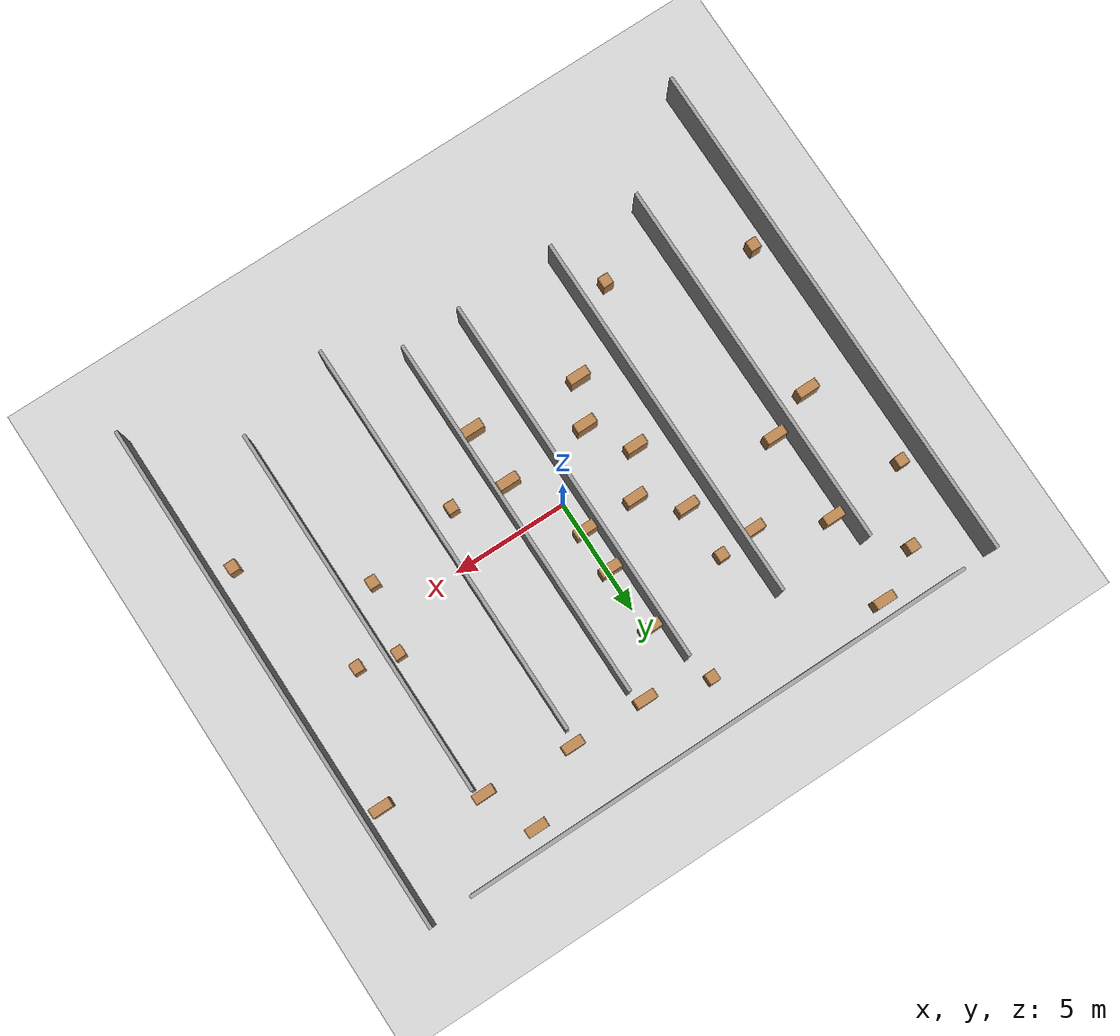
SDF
<sdf version="1.6">
 <world name="default">
  <light name="sun" type="directional">
   <pose>0 0 10 0 -0 0</pose>
   <diffuse>0.8 0.8 0.8 1</diffuse>
   <specular>0.2 0.2 0.2 1</specular>
   <attenuation>
    <range>1000</range>
    <constant>0.9</constant>
    <linear>0.01</linear>
    <quadratic>0.001</quadratic>
   </attenuation>
   <direction>-0.5 0.1 -0.9</direction>
  </light>
  <model name="ground_plane">
   <static>1</static>
   <link name="link">
    <collision name="collision">
     <geometry><plane><normal>0 0 1</normal><size>100 100</size></plane></geometry>
     <surface><friction><ode><mu>100</mu><mu2>50</mu2></ode></friction></surface>
    </collision>
    <visual name="visual">
     <cast_shadows>0</cast_shadows>
     <geometry><plane><normal>0 0 1</normal><size>100 100</size></plane></geometry>
     <material>
      <script><uri>file://media/materials/scripts/gazebo.material</uri><name>Gazebo/Grey</name></script>
     </material>
    </visual>
   </link>
  </model>
  <gravity>0 0 -9.8</gravity>
  <magnetic_field>6e-06 2.3e-05 -4.2e-05</magnetic_field>
  <atmosphere type="adiabatic"/>
  <physics name="default_physics" default="0" type="ode">
   <max_step_size>0.001</max_step_size>
   <real_time_factor>1</real_time_factor>
   <real_time_update_rate>1000</real_time_update_rate>
  </physics>
  <scene><ambient>0.4 0.4 0.4 1</ambient><background>0.7 0.7 0.7 1</background><shadows>1</shadows></scene>
  <audio><device>default</device></audio>
  <spherical_coordinates>
   <surface_model>EARTH_WGS84</surface_model>
   <latitude_deg>0</latitude_deg>
   <longitude_deg>0</longitude_deg>
   <elevation>0</elevation>
   <heading_deg>0</heading_deg>
  </spherical_coordinates>
  <model name="room14">
   <pose>0.127476 -0.35798 0 0 -0 0</pose>
   <link name="Wall_0">
    <collision name="Wall_0_Collision">
     <geometry><box><size>22.5 0.15 2.5</size></box></geometry>
     <pose>0 0 1.25 0 -0 0</pose>
    </collision>
    <visual name="Wall_0_Visual">
     <pose>0 0 1.25 0 -0 0</pose>
     <geometry><box><size>22.5 0.15 2.5</size></box></geometry>
     <material>
      <script><uri>file://media/materials/scripts/gazebo.material</uri><name>Gazebo/Grey</name></script>
      <ambient>1 1 1 1</ambient>
     </material>
     <meta><layer>0</layer></meta>
    </visual>
    <pose>-0.170741 11.1292 0 0 -0 0</pose>
   </link>
   <link name="Wall_10">
    <collision name="Wall_10_Collision">
     <geometry><box><size>16.25 0.15 2.5</size></box></geometry>
     <pose>0 0 1.25 0 -0 0</pose>
    </collision>
    <visual name="Wall_10_Visual">
     <pose>0 0 1.25 0 -0 0</pose>
     <geometry><box><size>16.25 0.15 2.5</size></box></geometry>
     <material>
      <script><uri>file://media/materials/scripts/gazebo.material</uri><name>Gazebo/Grey</name></script>
      <ambient>1 1 1 1</ambient>
     </material>
     <meta><layer>0</layer></meta>
    </visual>
    <pose>-0.774876 0.037064 0 0 -0 -1.5708</pose>
   </link>
   <link name="Wall_12">
    <collision name="Wall_12_Collision">
     <geometry><box><size>16 0.15 2.5</size></box></geometry>
     <pose>0 0 1.25 0 -0 0</pose>
    </collision>
    <visual name="Wall_12_Visual">
     <pose>0 0 1.25 0 -0 0</pose>
     <geometry><box><size>16 0.15 2.5</size></box></geometry>
     <material>
      <script><uri>file://media/materials/scripts/gazebo.material</uri><name>Gazebo/Grey</name></script>
      <ambient>1 1 1 1</ambient>
     </material>
     <meta><layer>0</layer></meta>
    </visual>
    <pose>1.86201 0.02328 0 0 -0 -1.5708</pose>
   </link>
   <link name="Wall_14">
    <collision name="Wall_14_Collision">
     <geometry><box><size>17.5 0.15 2.5</size></box></geometry>
     <pose>0 0 1.25 0 -0 0</pose>
    </collision>
    <visual name="Wall_14_Visual">
     <pose>0 0 1.25 0 -0 0</pose>
     <geometry><box><size>17.5 0.15 2.5</size></box></geometry>
     <material>
      <script><uri>file://media/materials/scripts/gazebo.material</uri><name>Gazebo/Grey</name></script>
      <ambient>1 1 1 1</ambient>
     </material>
     <meta><layer>0</layer></meta>
    </visual>
    <pose>4.63769 -0.819242 0 0 -0 -1.5708</pose>
   </link>
   <link name="Wall_16">
    <collision name="Wall_16_Collision">
     <geometry><box><size>16.25 0.15 2.5</size></box></geometry>
     <pose>0 0 1.25 0 -0 0</pose>
    </collision>
    <visual name="Wall_16_Visual">
     <pose>0 0 1.25 0 -0 0</pose>
     <geometry><box><size>16.25 0.15 2.5</size></box></geometry>
     <material>
      <script><uri>file://media/materials/scripts/gazebo.material</uri><name>Gazebo/Grey</name></script>
      <ambient>1 1 1 1</ambient>
     </material>
     <meta><layer>0</layer></meta>
    </visual>
    <pose>8.87059 -0.240503 0 0 -0 -1.5708</pose>
   </link>
   <link name="Wall_2">
    <collision name="Wall_2_Collision">
     <geometry><box><size>22.5 0.15 2.5</size></box></geometry>
     <pose>0 0 1.25 0 -0 0</pose>
    </collision>
    <visual name="Wall_2_Visual">
     <pose>0 0 1.25 0 -0 0</pose>
     <geometry><box><size>22.5 0.15 2.5</size></box></geometry>
     <material>
      <script><uri>file://media/materials/scripts/gazebo.material</uri><name>Gazebo/Grey</name></script>
      <ambient>1 1 1 1</ambient>
     </material>
     <meta><layer>0</layer></meta>
    </visual>
    <pose>-12.9184 -0.057826 0 0 -0 -1.5708</pose>
   </link>
   <link name="Wall_4">
    <collision name="Wall_4_Collision">
     <geometry><box><size>22.5 0.15 2.5</size></box></geometry>
     <pose>0 0 1.25 0 -0 0</pose>
    </collision>
    <visual name="Wall_4_Visual">
     <pose>0 0 1.25 0 -0 0</pose>
     <geometry><box><size>22.5 0.15 2.5</size></box></geometry>
     <material>
      <script><uri>file://media/materials/scripts/gazebo.material</uri><name>Gazebo/Grey</name></script>
      <ambient>1 1 1 1</ambient>
     </material>
     <meta><layer>0</layer></meta>
    </visual>
    <pose>12.9184 0.057827 0 0 -0 -1.5708</pose>
   </link>
   <link name="Wall_6">
    <collision name="Wall_6_Collision">
     <geometry><box><size>16.25 0.15 2.5</size></box></geometry>
     <pose>0 0 1.25 0 -0 0</pose>
    </collision>
    <visual name="Wall_6_Visual">
     <pose>0 0 1.25 0 -0 0</pose>
     <geometry><box><size>16.25 0.15 2.5</size></box></geometry>
     <material>
      <script><uri>file://media/materials/scripts/gazebo.material</uri><name>Gazebo/Grey</name></script>
      <ambient>1 1 1 1</ambient>
     </material>
     <meta><layer>0</layer></meta>
    </visual>
    <pose>-9.12503 0.013933 0 0 -0 -1.5708</pose>
   </link>
   <link name="Wall_8">
    <collision name="Wall_8_Collision">
     <geometry><box><size>16.25 0.15 2.5</size></box></geometry>
     <pose>0 0 1.25 0 -0 0</pose>
    </collision>
    <visual name="Wall_8_Visual">
     <pose>0 0 1.25 0 -0 0</pose>
     <geometry><box><size>16.25 0.15 2.5</size></box></geometry>
     <material>
      <script><uri>file://media/materials/scripts/gazebo.material</uri><name>Gazebo/Grey</name></script>
      <ambient>1 1 1 1</ambient>
     </material>
     <meta><layer>0</layer></meta>
    </visual>
    <pose>-5.14656 -0.078589 0 0 -0 -1.5708</pose>
   </link>
   <static>1</static>
  </model>
  <model name="bookshelf">
   <static>1</static>
   <link name="link">
    <inertial><mass>1</mass></inertial>
    <collision name="back">
     <pose>0 0.005 0.6 0 -0 0</pose>
     <geometry><box><size>0.9 0.01 1.2</size></box></geometry>
    </collision>
    <visual name="visual1">
     <pose>0 0.005 0.6 0 -0 0</pose>
     <geometry><box><size>0.9 0.01 1.2</size></box></geometry>
     <material>
      <script><uri>file://media/materials/scripts/gazebo.material</uri><name>Gazebo/Wood</name></script>
     </material>
    </visual>
    <collision name="left_side">
     <pose>0.45 -0.195 0.6 0 -0 0</pose>
     <geometry><box><size>0.02 0.4 1.2</size></box></geometry>
    </collision>
    <visual name="visual2">
     <pose>0.45 -0.195 0.6 0 -0 0</pose>
     <geometry><box><size>0.02 0.4 1.2</size></box></geometry>
     <material>
      <script><uri>file://media/materials/scripts/gazebo.material</uri><name>Gazebo/Wood</name></script>
     </material>
    </visual>
    <collision name="right_side">
     <pose>-0.45 -0.195 0.6 0 -0 0</pose>
     <geometry><box><size>0.02 0.4 1.2</size></box></geometry>
    </collision>
    <visual name="visual3">
     <pose>-0.45 -0.195 0.6 0 -0 0</pose>
     <geometry><box><size>0.02 0.4 1.2</size></box></geometry>
     <material>
      <script><uri>file://media/materials/scripts/gazebo.material</uri><name>Gazebo/Wood</name></script>
     </material>
    </visual>
    <collision name="bottom">
     <pose>0 -0.195 0.03 0 -0 0</pose>
     <geometry><box><size>0.88 0.4 0.06</size></box></geometry>
    </collision>
    <visual name="visual4">
     <pose>0 -0.195 0.03 0 -0 0</pose>
     <geometry><box><size>0.88 0.4 0.06</size></box></geometry>
     <material>
      <script><uri>file://media/materials/scripts/gazebo.material</uri><name>Gazebo/Wood</name></script>
     </material>
    </visual>
    <collision name="top">
     <pose>0 -0.195 1.19 0 -0 0</pose>
     <geometry><box><size>0.88 0.4 0.02</size></box></geometry>
    </collision>
    <visual name="visual5">
     <pose>0 -0.195 1.19 0 -0 0</pose>
     <geometry><box><size>0.88 0.4 0.02</size></box></geometry>
     <material>
      <script><uri>file://media/materials/scripts/gazebo.material</uri><name>Gazebo/Wood</name></script>
     </material>
    </visual>
    <collision name="low_shelf">
     <pose>0 -0.195 0.43 0 -0 0</pose>
     <geometry><box><size>0.88 0.4 0.02</size></box></geometry>
    </collision>
    <visual name="visual6">
     <pose>0 -0.195 0.43 0 -0 0</pose>
     <geometry><box><size>0.88 0.4 0.02</size></box></geometry>
     <material>
      <script><uri>file://media/materials/scripts/gazebo.material</uri><name>Gazebo/Wood</name></script>
     </material>
    </visual>
    <collision name="high_shelf">
     <pose>0 -0.195 0.8 0 -0 0</pose>
     <geometry><box><size>0.88 0.4 0.02</size></box></geometry>
    </collision>
    <visual name="visual7">
     <pose>0 -0.195 0.8 0 -0 0</pose>
     <geometry><box><size>0.88 0.4 0.02</size></box></geometry>
     <material>
      <script><uri>file://media/materials/scripts/gazebo.material</uri><name>Gazebo/Wood</name></script>
     </material>
    </visual>
   </link>
   <pose>-8.52766 6.49554 0 0 -0 0</pose>
  </model>
  <model name="bookshelf_0">
   <static>1</static>
   <link name="link">
    <inertial><mass>1</mass></inertial>
    <collision name="back">
     <pose>0 0.005 0.6 0 -0 0</pose>
     <geometry><box><size>0.9 0.01 1.2</size></box></geometry>
    </collision>
    <visual name="visual1">
     <pose>0 0.005 0.6 0 -0 0</pose>
     <geometry><box><size>0.9 0.01 1.2</size></box></geometry>
     <material>
      <script><uri>file://media/materials/scripts/gazebo.material</uri><name>Gazebo/Wood</name></script>
     </material>
    </visual>
    <collision name="left_side">
     <pose>0.45 -0.195 0.6 0 -0 0</pose>
     <geometry><box><size>0.02 0.4 1.2</size></box></geometry>
    </collision>
    <visual name="visual2">
     <pose>0.45 -0.195 0.6 0 -0 0</pose>
     <geometry><box><size>0.02 0.4 1.2</size></box></geometry>
     <material>
      <script><uri>file://media/materials/scripts/gazebo.material</uri><name>Gazebo/Wood</name></script>
     </material>
    </visual>
    <collision name="right_side">
     <pose>-0.45 -0.195 0.6 0 -0 0</pose>
     <geometry><box><size>0.02 0.4 1.2</size></box></geometry>
    </collision>
    <visual name="visual3">
     <pose>-0.45 -0.195 0.6 0 -0 0</pose>
     <geometry><box><size>0.02 0.4 1.2</size></box></geometry>
     <material>
      <script><uri>file://media/materials/scripts/gazebo.material</uri><name>Gazebo/Wood</name></script>
     </material>
    </visual>
    <collision name="bottom">
     <pose>0 -0.195 0.03 0 -0 0</pose>
     <geometry><box><size>0.88 0.4 0.06</size></box></geometry>
    </collision>
    <visual name="visual4">
     <pose>0 -0.195 0.03 0 -0 0</pose>
     <geometry><box><size>0.88 0.4 0.06</size></box></geometry>
     <material>
      <script><uri>file://media/materials/scripts/gazebo.material</uri><name>Gazebo/Wood</name></script>
     </material>
    </visual>
    <collision name="top">
     <pose>0 -0.195 1.19 0 -0 0</pose>
     <geometry><box><size>0.88 0.4 0.02</size></box></geometry>
    </collision>
    <visual name="visual5">
     <pose>0 -0.195 1.19 0 -0 0</pose>
     <geometry><box><size>0.88 0.4 0.02</size></box></geometry>
     <material>
      <script><uri>file://media/materials/scripts/gazebo.material</uri><name>Gazebo/Wood</name></script>
     </material>
    </visual>
    <collision name="low_shelf">
     <pose>0 -0.195 0.43 0 -0 0</pose>
     <geometry><box><size>0.88 0.4 0.02</size></box></geometry>
    </collision>
    <visual name="visual6">
     <pose>0 -0.195 0.43 0 -0 0</pose>
     <geometry><box><size>0.88 0.4 0.02</size></box></geometry>
     <material>
      <script><uri>file://media/materials/scripts/gazebo.material</uri><name>Gazebo/Wood</name></script>
     </material>
    </visual>
    <collision name="high_shelf">
     <pose>0 -0.195 0.8 0 -0 0</pose>
     <geometry><box><size>0.88 0.4 0.02</size></box></geometry>
    </collision>
    <visual name="visual7">
     <pose>0 -0.195 0.8 0 -0 0</pose>
     <geometry><box><size>0.88 0.4 0.02</size></box></geometry>
     <material>
      <script><uri>file://media/materials/scripts/gazebo.material</uri><name>Gazebo/Wood</name></script>
     </material>
    </visual>
   </link>
   <pose>-8.40442 2.58916 0 0 -0 0</pose>
  </model>
  <model name="bookshelf_1">
   <static>1</static>
   <link name="link">
    <inertial><mass>1</mass></inertial>
    <collision name="back">
     <pose>0 0.005 0.6 0 -0 0</pose>
     <geometry><box><size>0.9 0.01 1.2</size></box></geometry>
    </collision>
    <visual name="visual1">
     <pose>0 0.005 0.6 0 -0 0</pose>
     <geometry><box><size>0.9 0.01 1.2</size></box></geometry>
     <material>
      <script><uri>file://media/materials/scripts/gazebo.material</uri><name>Gazebo/Wood</name></script>
     </material>
    </visual>
    <collision name="left_side">
     <pose>0.45 -0.195 0.6 0 -0 0</pose>
     <geometry><box><size>0.02 0.4 1.2</size></box></geometry>
    </collision>
    <visual name="visual2">
     <pose>0.45 -0.195 0.6 0 -0 0</pose>
     <geometry><box><size>0.02 0.4 1.2</size></box></geometry>
     <material>
      <script><uri>file://media/materials/scripts/gazebo.material</uri><name>Gazebo/Wood</name></script>
     </material>
    </visual>
    <collision name="right_side">
     <pose>-0.45 -0.195 0.6 0 -0 0</pose>
     <geometry><box><size>0.02 0.4 1.2</size></box></geometry>
    </collision>
    <visual name="visual3">
     <pose>-0.45 -0.195 0.6 0 -0 0</pose>
     <geometry><box><size>0.02 0.4 1.2</size></box></geometry>
     <material>
      <script><uri>file://media/materials/scripts/gazebo.material</uri><name>Gazebo/Wood</name></script>
     </material>
    </visual>
    <collision name="bottom">
     <pose>0 -0.195 0.03 0 -0 0</pose>
     <geometry><box><size>0.88 0.4 0.06</size></box></geometry>
    </collision>
    <visual name="visual4">
     <pose>0 -0.195 0.03 0 -0 0</pose>
     <geometry><box><size>0.88 0.4 0.06</size></box></geometry>
     <material>
      <script><uri>file://media/materials/scripts/gazebo.material</uri><name>Gazebo/Wood</name></script>
     </material>
    </visual>
    <collision name="top">
     <pose>0 -0.195 1.19 0 -0 0</pose>
     <geometry><box><size>0.88 0.4 0.02</size></box></geometry>
    </collision>
    <visual name="visual5">
     <pose>0 -0.195 1.19 0 -0 0</pose>
     <geometry><box><size>0.88 0.4 0.02</size></box></geometry>
     <material>
      <script><uri>file://media/materials/scripts/gazebo.material</uri><name>Gazebo/Wood</name></script>
     </material>
    </visual>
    <collision name="low_shelf">
     <pose>0 -0.195 0.43 0 -0 0</pose>
     <geometry><box><size>0.88 0.4 0.02</size></box></geometry>
    </collision>
    <visual name="visual6">
     <pose>0 -0.195 0.43 0 -0 0</pose>
     <geometry><box><size>0.88 0.4 0.02</size></box></geometry>
     <material>
      <script><uri>file://media/materials/scripts/gazebo.material</uri><name>Gazebo/Wood</name></script>
     </material>
    </visual>
    <collision name="high_shelf">
     <pose>0 -0.195 0.8 0 -0 0</pose>
     <geometry><box><size>0.88 0.4 0.02</size></box></geometry>
    </collision>
    <visual name="visual7">
     <pose>0 -0.195 0.8 0 -0 0</pose>
     <geometry><box><size>0.88 0.4 0.02</size></box></geometry>
     <material>
      <script><uri>file://media/materials/scripts/gazebo.material</uri><name>Gazebo/Wood</name></script>
     </material>
    </visual>
   </link>
   <pose>-5.61984 5.19296 0 0 -0 0</pose>
  </model>
  <model name="bookshelf_2">
   <static>1</static>
   <link name="link">
    <inertial><mass>1</mass></inertial>
    <collision name="back">
     <pose>0 0.005 0.6 0 -0 0</pose>
     <geometry><box><size>0.9 0.01 1.2</size></box></geometry>
    </collision>
    <visual name="visual1">
     <pose>0 0.005 0.6 0 -0 0</pose>
     <geometry><box><size>0.9 0.01 1.2</size></box></geometry>
     <material>
      <script><uri>file://media/materials/scripts/gazebo.material</uri><name>Gazebo/Wood</name></script>
     </material>
    </visual>
    <collision name="left_side">
     <pose>0.45 -0.195 0.6 0 -0 0</pose>
     <geometry><box><size>0.02 0.4 1.2</size></box></geometry>
    </collision>
    <visual name="visual2">
     <pose>0.45 -0.195 0.6 0 -0 0</pose>
     <geometry><box><size>0.02 0.4 1.2</size></box></geometry>
     <material>
      <script><uri>file://media/materials/scripts/gazebo.material</uri><name>Gazebo/Wood</name></script>
     </material>
    </visual>
    <collision name="right_side">
     <pose>-0.45 -0.195 0.6 0 -0 0</pose>
     <geometry><box><size>0.02 0.4 1.2</size></box></geometry>
    </collision>
    <visual name="visual3">
     <pose>-0.45 -0.195 0.6 0 -0 0</pose>
     <geometry><box><size>0.02 0.4 1.2</size></box></geometry>
     <material>
      <script><uri>file://media/materials/scripts/gazebo.material</uri><name>Gazebo/Wood</name></script>
     </material>
    </visual>
    <collision name="bottom">
     <pose>0 -0.195 0.03 0 -0 0</pose>
     <geometry><box><size>0.88 0.4 0.06</size></box></geometry>
    </collision>
    <visual name="visual4">
     <pose>0 -0.195 0.03 0 -0 0</pose>
     <geometry><box><size>0.88 0.4 0.06</size></box></geometry>
     <material>
      <script><uri>file://media/materials/scripts/gazebo.material</uri><name>Gazebo/Wood</name></script>
     </material>
    </visual>
    <collision name="top">
     <pose>0 -0.195 1.19 0 -0 0</pose>
     <geometry><box><size>0.88 0.4 0.02</size></box></geometry>
    </collision>
    <visual name="visual5">
     <pose>0 -0.195 1.19 0 -0 0</pose>
     <geometry><box><size>0.88 0.4 0.02</size></box></geometry>
     <material>
      <script><uri>file://media/materials/scripts/gazebo.material</uri><name>Gazebo/Wood</name></script>
     </material>
    </visual>
    <collision name="low_shelf">
     <pose>0 -0.195 0.43 0 -0 0</pose>
     <geometry><box><size>0.88 0.4 0.02</size></box></geometry>
    </collision>
    <visual name="visual6">
     <pose>0 -0.195 0.43 0 -0 0</pose>
     <geometry><box><size>0.88 0.4 0.02</size></box></geometry>
     <material>
      <script><uri>file://media/materials/scripts/gazebo.material</uri><name>Gazebo/Wood</name></script>
     </material>
    </visual>
    <collision name="high_shelf">
     <pose>0 -0.195 0.8 0 -0 0</pose>
     <geometry><box><size>0.88 0.4 0.02</size></box></geometry>
    </collision>
    <visual name="visual7">
     <pose>0 -0.195 0.8 0 -0 0</pose>
     <geometry><box><size>0.88 0.4 0.02</size></box></geometry>
     <material>
      <script><uri>file://media/materials/scripts/gazebo.material</uri><name>Gazebo/Wood</name></script>
     </material>
    </visual>
   </link>
   <pose>-0.130178 6.17554 0 0 -0 0</pose>
  </model>
  <model name="bookshelf_3">
   <static>1</static>
   <link name="link">
    <inertial><mass>1</mass></inertial>
    <collision name="back">
     <pose>0 0.005 0.6 0 -0 0</pose>
     <geometry><box><size>0.9 0.01 1.2</size></box></geometry>
    </collision>
    <visual name="visual1">
     <pose>0 0.005 0.6 0 -0 0</pose>
     <geometry><box><size>0.9 0.01 1.2</size></box></geometry>
     <material>
      <script><uri>file://media/materials/scripts/gazebo.material</uri><name>Gazebo/Wood</name></script>
     </material>
    </visual>
    <collision name="left_side">
     <pose>0.45 -0.195 0.6 0 -0 0</pose>
     <geometry><box><size>0.02 0.4 1.2</size></box></geometry>
    </collision>
    <visual name="visual2">
     <pose>0.45 -0.195 0.6 0 -0 0</pose>
     <geometry><box><size>0.02 0.4 1.2</size></box></geometry>
     <material>
      <script><uri>file://media/materials/scripts/gazebo.material</uri><name>Gazebo/Wood</name></script>
     </material>
    </visual>
    <collision name="right_side">
     <pose>-0.45 -0.195 0.6 0 -0 0</pose>
     <geometry><box><size>0.02 0.4 1.2</size></box></geometry>
    </collision>
    <visual name="visual3">
     <pose>-0.45 -0.195 0.6 0 -0 0</pose>
     <geometry><box><size>0.02 0.4 1.2</size></box></geometry>
     <material>
      <script><uri>file://media/materials/scripts/gazebo.material</uri><name>Gazebo/Wood</name></script>
     </material>
    </visual>
    <collision name="bottom">
     <pose>0 -0.195 0.03 0 -0 0</pose>
     <geometry><box><size>0.88 0.4 0.06</size></box></geometry>
    </collision>
    <visual name="visual4">
     <pose>0 -0.195 0.03 0 -0 0</pose>
     <geometry><box><size>0.88 0.4 0.06</size></box></geometry>
     <material>
      <script><uri>file://media/materials/scripts/gazebo.material</uri><name>Gazebo/Wood</name></script>
     </material>
    </visual>
    <collision name="top">
     <pose>0 -0.195 1.19 0 -0 0</pose>
     <geometry><box><size>0.88 0.4 0.02</size></box></geometry>
    </collision>
    <visual name="visual5">
     <pose>0 -0.195 1.19 0 -0 0</pose>
     <geometry><box><size>0.88 0.4 0.02</size></box></geometry>
     <material>
      <script><uri>file://media/materials/scripts/gazebo.material</uri><name>Gazebo/Wood</name></script>
     </material>
    </visual>
    <collision name="low_shelf">
     <pose>0 -0.195 0.43 0 -0 0</pose>
     <geometry><box><size>0.88 0.4 0.02</size></box></geometry>
    </collision>
    <visual name="visual6">
     <pose>0 -0.195 0.43 0 -0 0</pose>
     <geometry><box><size>0.88 0.4 0.02</size></box></geometry>
     <material>
      <script><uri>file://media/materials/scripts/gazebo.material</uri><name>Gazebo/Wood</name></script>
     </material>
    </visual>
    <collision name="high_shelf">
     <pose>0 -0.195 0.8 0 -0 0</pose>
     <geometry><box><size>0.88 0.4 0.02</size></box></geometry>
    </collision>
    <visual name="visual7">
     <pose>0 -0.195 0.8 0 -0 0</pose>
     <geometry><box><size>0.88 0.4 0.02</size></box></geometry>
     <material>
      <script><uri>file://media/materials/scripts/gazebo.material</uri><name>Gazebo/Wood</name></script>
     </material>
    </visual>
   </link>
   <pose>-0.095564 3.42207 0 0 -0 0</pose>
  </model>
  <model name="bookshelf_4">
   <static>1</static>
   <link name="link">
    <inertial><mass>1</mass></inertial>
    <collision name="back">
     <pose>0 0.005 0.6 0 -0 0</pose>
     <geometry><box><size>0.9 0.01 1.2</size></box></geometry>
    </collision>
    <visual name="visual1">
     <pose>0 0.005 0.6 0 -0 0</pose>
     <geometry><box><size>0.9 0.01 1.2</size></box></geometry>
     <material>
      <script><uri>file://media/materials/scripts/gazebo.material</uri><name>Gazebo/Wood</name></script>
     </material>
    </visual>
    <collision name="left_side">
     <pose>0.45 -0.195 0.6 0 -0 0</pose>
     <geometry><box><size>0.02 0.4 1.2</size></box></geometry>
    </collision>
    <visual name="visual2">
     <pose>0.45 -0.195 0.6 0 -0 0</pose>
     <geometry><box><size>0.02 0.4 1.2</size></box></geometry>
     <material>
      <script><uri>file://media/materials/scripts/gazebo.material</uri><name>Gazebo/Wood</name></script>
     </material>
    </visual>
    <collision name="right_side">
     <pose>-0.45 -0.195 0.6 0 -0 0</pose>
     <geometry><box><size>0.02 0.4 1.2</size></box></geometry>
    </collision>
    <visual name="visual3">
     <pose>-0.45 -0.195 0.6 0 -0 0</pose>
     <geometry><box><size>0.02 0.4 1.2</size></box></geometry>
     <material>
      <script><uri>file://media/materials/scripts/gazebo.material</uri><name>Gazebo/Wood</name></script>
     </material>
    </visual>
    <collision name="bottom">
     <pose>0 -0.195 0.03 0 -0 0</pose>
     <geometry><box><size>0.88 0.4 0.06</size></box></geometry>
    </collision>
    <visual name="visual4">
     <pose>0 -0.195 0.03 0 -0 0</pose>
     <geometry><box><size>0.88 0.4 0.06</size></box></geometry>
     <material>
      <script><uri>file://media/materials/scripts/gazebo.material</uri><name>Gazebo/Wood</name></script>
     </material>
    </visual>
    <collision name="top">
     <pose>0 -0.195 1.19 0 -0 0</pose>
     <geometry><box><size>0.88 0.4 0.02</size></box></geometry>
    </collision>
    <visual name="visual5">
     <pose>0 -0.195 1.19 0 -0 0</pose>
     <geometry><box><size>0.88 0.4 0.02</size></box></geometry>
     <material>
      <script><uri>file://media/materials/scripts/gazebo.material</uri><name>Gazebo/Wood</name></script>
     </material>
    </visual>
    <collision name="low_shelf">
     <pose>0 -0.195 0.43 0 -0 0</pose>
     <geometry><box><size>0.88 0.4 0.02</size></box></geometry>
    </collision>
    <visual name="visual6">
     <pose>0 -0.195 0.43 0 -0 0</pose>
     <geometry><box><size>0.88 0.4 0.02</size></box></geometry>
     <material>
      <script><uri>file://media/materials/scripts/gazebo.material</uri><name>Gazebo/Wood</name></script>
     </material>
    </visual>
    <collision name="high_shelf">
     <pose>0 -0.195 0.8 0 -0 0</pose>
     <geometry><box><size>0.88 0.4 0.02</size></box></geometry>
    </collision>
    <visual name="visual7">
     <pose>0 -0.195 0.8 0 -0 0</pose>
     <geometry><box><size>0.88 0.4 0.02</size></box></geometry>
     <material>
      <script><uri>file://media/materials/scripts/gazebo.material</uri><name>Gazebo/Wood</name></script>
     </material>
    </visual>
   </link>
   <pose>-0.10659 1.61243 0 0 -0 0</pose>
  </model>
  <model name="bookshelf_5">
   <static>1</static>
   <link name="link">
    <inertial><mass>1</mass></inertial>
    <collision name="back">
     <pose>0 0.005 0.6 0 -0 0</pose>
     <geometry><box><size>0.9 0.01 1.2</size></box></geometry>
    </collision>
    <visual name="visual1">
     <pose>0 0.005 0.6 0 -0 0</pose>
     <geometry><box><size>0.9 0.01 1.2</size></box></geometry>
     <material>
      <script><uri>file://media/materials/scripts/gazebo.material</uri><name>Gazebo/Wood</name></script>
     </material>
    </visual>
    <collision name="left_side">
     <pose>0.45 -0.195 0.6 0 -0 0</pose>
     <geometry><box><size>0.02 0.4 1.2</size></box></geometry>
    </collision>
    <visual name="visual2">
     <pose>0.45 -0.195 0.6 0 -0 0</pose>
     <geometry><box><size>0.02 0.4 1.2</size></box></geometry>
     <material>
      <script><uri>file://media/materials/scripts/gazebo.material</uri><name>Gazebo/Wood</name></script>
     </material>
    </visual>
    <collision name="right_side">
     <pose>-0.45 -0.195 0.6 0 -0 0</pose>
     <geometry><box><size>0.02 0.4 1.2</size></box></geometry>
    </collision>
    <visual name="visual3">
     <pose>-0.45 -0.195 0.6 0 -0 0</pose>
     <geometry><box><size>0.02 0.4 1.2</size></box></geometry>
     <material>
      <script><uri>file://media/materials/scripts/gazebo.material</uri><name>Gazebo/Wood</name></script>
     </material>
    </visual>
    <collision name="bottom">
     <pose>0 -0.195 0.03 0 -0 0</pose>
     <geometry><box><size>0.88 0.4 0.06</size></box></geometry>
    </collision>
    <visual name="visual4">
     <pose>0 -0.195 0.03 0 -0 0</pose>
     <geometry><box><size>0.88 0.4 0.06</size></box></geometry>
     <material>
      <script><uri>file://media/materials/scripts/gazebo.material</uri><name>Gazebo/Wood</name></script>
     </material>
    </visual>
    <collision name="top">
     <pose>0 -0.195 1.19 0 -0 0</pose>
     <geometry><box><size>0.88 0.4 0.02</size></box></geometry>
    </collision>
    <visual name="visual5">
     <pose>0 -0.195 1.19 0 -0 0</pose>
     <geometry><box><size>0.88 0.4 0.02</size></box></geometry>
     <material>
      <script><uri>file://media/materials/scripts/gazebo.material</uri><name>Gazebo/Wood</name></script>
     </material>
    </visual>
    <collision name="low_shelf">
     <pose>0 -0.195 0.43 0 -0 0</pose>
     <geometry><box><size>0.88 0.4 0.02</size></box></geometry>
    </collision>
    <visual name="visual6">
     <pose>0 -0.195 0.43 0 -0 0</pose>
     <geometry><box><size>0.88 0.4 0.02</size></box></geometry>
     <material>
      <script><uri>file://media/materials/scripts/gazebo.material</uri><name>Gazebo/Wood</name></script>
     </material>
    </visual>
    <collision name="high_shelf">
     <pose>0 -0.195 0.8 0 -0 0</pose>
     <geometry><box><size>0.88 0.4 0.02</size></box></geometry>
    </collision>
    <visual name="visual7">
     <pose>0 -0.195 0.8 0 -0 0</pose>
     <geometry><box><size>0.88 0.4 0.02</size></box></geometry>
     <material>
      <script><uri>file://media/materials/scripts/gazebo.material</uri><name>Gazebo/Wood</name></script>
     </material>
    </visual>
   </link>
   <pose>1.36039 -1.63052 0 0 -0 0</pose>
  </model>
  <model name="bookshelf_6">
   <static>1</static>
   <link name="link">
    <inertial><mass>1</mass></inertial>
    <collision name="back">
     <pose>0 0.005 0.6 0 -0 0</pose>
     <geometry><box><size>0.9 0.01 1.2</size></box></geometry>
    </collision>
    <visual name="visual1">
     <pose>0 0.005 0.6 0 -0 0</pose>
     <geometry><box><size>0.9 0.01 1.2</size></box></geometry>
     <material>
      <script><uri>file://media/materials/scripts/gazebo.material</uri><name>Gazebo/Wood</name></script>
     </material>
    </visual>
    <collision name="left_side">
     <pose>0.45 -0.195 0.6 0 -0 0</pose>
     <geometry><box><size>0.02 0.4 1.2</size></box></geometry>
    </collision>
    <visual name="visual2">
     <pose>0.45 -0.195 0.6 0 -0 0</pose>
     <geometry><box><size>0.02 0.4 1.2</size></box></geometry>
     <material>
      <script><uri>file://media/materials/scripts/gazebo.material</uri><name>Gazebo/Wood</name></script>
     </material>
    </visual>
    <collision name="right_side">
     <pose>-0.45 -0.195 0.6 0 -0 0</pose>
     <geometry><box><size>0.02 0.4 1.2</size></box></geometry>
    </collision>
    <visual name="visual3">
     <pose>-0.45 -0.195 0.6 0 -0 0</pose>
     <geometry><box><size>0.02 0.4 1.2</size></box></geometry>
     <material>
      <script><uri>file://media/materials/scripts/gazebo.material</uri><name>Gazebo/Wood</name></script>
     </material>
    </visual>
    <collision name="bottom">
     <pose>0 -0.195 0.03 0 -0 0</pose>
     <geometry><box><size>0.88 0.4 0.06</size></box></geometry>
    </collision>
    <visual name="visual4">
     <pose>0 -0.195 0.03 0 -0 0</pose>
     <geometry><box><size>0.88 0.4 0.06</size></box></geometry>
     <material>
      <script><uri>file://media/materials/scripts/gazebo.material</uri><name>Gazebo/Wood</name></script>
     </material>
    </visual>
    <collision name="top">
     <pose>0 -0.195 1.19 0 -0 0</pose>
     <geometry><box><size>0.88 0.4 0.02</size></box></geometry>
    </collision>
    <visual name="visual5">
     <pose>0 -0.195 1.19 0 -0 0</pose>
     <geometry><box><size>0.88 0.4 0.02</size></box></geometry>
     <material>
      <script><uri>file://media/materials/scripts/gazebo.material</uri><name>Gazebo/Wood</name></script>
     </material>
    </visual>
    <collision name="low_shelf">
     <pose>0 -0.195 0.43 0 -0 0</pose>
     <geometry><box><size>0.88 0.4 0.02</size></box></geometry>
    </collision>
    <visual name="visual6">
     <pose>0 -0.195 0.43 0 -0 0</pose>
     <geometry><box><size>0.88 0.4 0.02</size></box></geometry>
     <material>
      <script><uri>file://media/materials/scripts/gazebo.material</uri><name>Gazebo/Wood</name></script>
     </material>
    </visual>
    <collision name="high_shelf">
     <pose>0 -0.195 0.8 0 -0 0</pose>
     <geometry><box><size>0.88 0.4 0.02</size></box></geometry>
    </collision>
    <visual name="visual7">
     <pose>0 -0.195 0.8 0 -0 0</pose>
     <geometry><box><size>0.88 0.4 0.02</size></box></geometry>
     <material>
      <script><uri>file://media/materials/scripts/gazebo.material</uri><name>Gazebo/Wood</name></script>
     </material>
    </visual>
   </link>
   <pose>1.39235 -4.15246 0 0 -0 0</pose>
  </model>
  <model name="bookshelf_7">
   <static>1</static>
   <link name="link">
    <inertial><mass>1</mass></inertial>
    <collision name="back">
     <pose>0 0.005 0.6 0 -0 0</pose>
     <geometry><box><size>0.9 0.01 1.2</size></box></geometry>
    </collision>
    <visual name="visual1">
     <pose>0 0.005 0.6 0 -0 0</pose>
     <geometry><box><size>0.9 0.01 1.2</size></box></geometry>
     <material>
      <script><uri>file://media/materials/scripts/gazebo.material</uri><name>Gazebo/Wood</name></script>
     </material>
    </visual>
    <collision name="left_side">
     <pose>0.45 -0.195 0.6 0 -0 0</pose>
     <geometry><box><size>0.02 0.4 1.2</size></box></geometry>
    </collision>
    <visual name="visual2">
     <pose>0.45 -0.195 0.6 0 -0 0</pose>
     <geometry><box><size>0.02 0.4 1.2</size></box></geometry>
     <material>
      <script><uri>file://media/materials/scripts/gazebo.material</uri><name>Gazebo/Wood</name></script>
     </material>
    </visual>
    <collision name="right_side">
     <pose>-0.45 -0.195 0.6 0 -0 0</pose>
     <geometry><box><size>0.02 0.4 1.2</size></box></geometry>
    </collision>
    <visual name="visual3">
     <pose>-0.45 -0.195 0.6 0 -0 0</pose>
     <geometry><box><size>0.02 0.4 1.2</size></box></geometry>
     <material>
      <script><uri>file://media/materials/scripts/gazebo.material</uri><name>Gazebo/Wood</name></script>
     </material>
    </visual>
    <collision name="bottom">
     <pose>0 -0.195 0.03 0 -0 0</pose>
     <geometry><box><size>0.88 0.4 0.06</size></box></geometry>
    </collision>
    <visual name="visual4">
     <pose>0 -0.195 0.03 0 -0 0</pose>
     <geometry><box><size>0.88 0.4 0.06</size></box></geometry>
     <material>
      <script><uri>file://media/materials/scripts/gazebo.material</uri><name>Gazebo/Wood</name></script>
     </material>
    </visual>
    <collision name="top">
     <pose>0 -0.195 1.19 0 -0 0</pose>
     <geometry><box><size>0.88 0.4 0.02</size></box></geometry>
    </collision>
    <visual name="visual5">
     <pose>0 -0.195 1.19 0 -0 0</pose>
     <geometry><box><size>0.88 0.4 0.02</size></box></geometry>
     <material>
      <script><uri>file://media/materials/scripts/gazebo.material</uri><name>Gazebo/Wood</name></script>
     </material>
    </visual>
    <collision name="low_shelf">
     <pose>0 -0.195 0.43 0 -0 0</pose>
     <geometry><box><size>0.88 0.4 0.02</size></box></geometry>
    </collision>
    <visual name="visual6">
     <pose>0 -0.195 0.43 0 -0 0</pose>
     <geometry><box><size>0.88 0.4 0.02</size></box></geometry>
     <material>
      <script><uri>file://media/materials/scripts/gazebo.material</uri><name>Gazebo/Wood</name></script>
     </material>
    </visual>
    <collision name="high_shelf">
     <pose>0 -0.195 0.8 0 -0 0</pose>
     <geometry><box><size>0.88 0.4 0.02</size></box></geometry>
    </collision>
    <visual name="visual7">
     <pose>0 -0.195 0.8 0 -0 0</pose>
     <geometry><box><size>0.88 0.4 0.02</size></box></geometry>
     <material>
      <script><uri>file://media/materials/scripts/gazebo.material</uri><name>Gazebo/Wood</name></script>
     </material>
    </visual>
   </link>
   <pose>12.3093 6.29866 0 0 -0 0</pose>
  </model>
  <model name="cabinet">
   <static>1</static>
   <link name="cabinet_bottom_plate">
    <inertial>
     <pose>0 0 -1 0 -0 0</pose>
     <inertia><ixx>2.05</ixx><ixy>0</ixy><ixz>0</ixz><iyy>2.05</iyy><iyz>0</iyz><izz>2.05</izz></inertia>
     <mass>25</mass>
    </inertial>
    <collision name="cabinet_bottom_plate_geom">
     <pose>0 0 0.01 0 -0 0</pose>
     <geometry><box><size>0.45 0.45 0.02</size></box></geometry>
    </collision>
    <visual name="cabinet_bottom_plate_geom_visual">
     <pose>0 0 0.01 0 -0 0</pose>
     <geometry><box><size>0.45 0.45 0.02</size></box></geometry>
     <material>
      <script><uri>file://media/materials/scripts/gazebo.material</uri><name>Gazebo/Wood</name></script>
     </material>
    </visual>
    <collision name="cabinet_bottom_plate_geom_cabinet_back_plate">
     <pose>0.235 0 0.51 0 -0 0</pose>
     <geometry><box><size>0.02 0.45 1.02</size></box></geometry>
    </collision>
    <visual name="cabinet_bottom_plate_geom_cabinet_back_plate_visual">
     <pose>0.235 0 0.51 0 -0 0</pose>
     <geometry><box><size>0.02 0.45 1.02</size></box></geometry>
     <material>
      <script><uri>file://media/materials/scripts/gazebo.material</uri><name>Gazebo/Wood</name></script>
     </material>
    </visual>
    <collision name="cabinet_bottom_plate_geom_cabinet_left_plate">
     <pose>0 0.235 0.51 0 -0 0</pose>
     <geometry><box><size>0.45 0.02 1.02</size></box></geometry>
    </collision>
    <visual name="cabinet_bottom_plate_geom_cabinet_left_plate_visual">
     <pose>0 0.235 0.51 0 -0 0</pose>
     <geometry><box><size>0.45 0.02 1.02</size></box></geometry>
     <material>
      <script><uri>file://media/materials/scripts/gazebo.material</uri><name>Gazebo/Wood</name></script>
     </material>
    </visual>
    <collision name="cabinet_bottom_plate_geom_cabinet_middle_plate">
     <pose>0 0 0.51 0 -0 0</pose>
     <geometry><box><size>0.45 0.45 0.02</size></box></geometry>
    </collision>
    <visual name="cabinet_bottom_plate_geom_cabinet_middle_plate_visual">
     <pose>0 0 0.51 0 -0 0</pose>
     <geometry><box><size>0.45 0.45 0.02</size></box></geometry>
     <material>
      <script><uri>file://media/materials/scripts/gazebo.material</uri><name>Gazebo/Wood</name></script>
     </material>
    </visual>
    <collision name="cabinet_bottom_plate_geom_cabinet_right_plate">
     <pose>0 -0.235 0.51 0 -0 0</pose>
     <geometry><box><size>0.45 0.02 1.02</size></box></geometry>
    </collision>
    <visual name="cabinet_bottom_plate_geom_cabinet_right_plate_visual">
     <pose>0 -0.235 0.51 0 -0 0</pose>
     <geometry><box><size>0.45 0.02 1.02</size></box></geometry>
     <material>
      <script><uri>file://media/materials/scripts/gazebo.material</uri><name>Gazebo/Wood</name></script>
     </material>
    </visual>
    <collision name="cabinet_bottom_plate_geom_cabinet_top_plate">
     <pose>0 0 1.01 0 -0 0</pose>
     <geometry><box><size>0.45 0.45 0.02</size></box></geometry>
    </collision>
    <visual name="cabinet_bottom_plate_geom_cabinet_top_plate_visual">
     <pose>0 0 1.01 0 -0 0</pose>
     <geometry><box><size>0.45 0.45 0.02</size></box></geometry>
     <material>
      <script><uri>file://media/materials/scripts/gazebo.material</uri><name>Gazebo/Wood</name></script>
     </material>
    </visual>
   </link>
   <pose>-4.04654 5.14765 0 0 -0 0</pose>
  </model>
  <model name="cabinet_0">
   <static>1</static>
   <link name="cabinet_bottom_plate">
    <inertial>
     <pose>0 0 -1 0 -0 0</pose>
     <inertia><ixx>2.05</ixx><ixy>0</ixy><ixz>0</ixz><iyy>2.05</iyy><iyz>0</iyz><izz>2.05</izz></inertia>
     <mass>25</mass>
    </inertial>
    <collision name="cabinet_bottom_plate_geom">
     <pose>0 0 0.01 0 -0 0</pose>
     <geometry><box><size>0.45 0.45 0.02</size></box></geometry>
    </collision>
    <visual name="cabinet_bottom_plate_geom_visual">
     <pose>0 0 0.01 0 -0 0</pose>
     <geometry><box><size>0.45 0.45 0.02</size></box></geometry>
     <material>
      <script><uri>file://media/materials/scripts/gazebo.material</uri><name>Gazebo/Wood</name></script>
     </material>
    </visual>
    <collision name="cabinet_bottom_plate_geom_cabinet_back_plate">
     <pose>0.235 0 0.51 0 -0 0</pose>
     <geometry><box><size>0.02 0.45 1.02</size></box></geometry>
    </collision>
    <visual name="cabinet_bottom_plate_geom_cabinet_back_plate_visual">
     <pose>0.235 0 0.51 0 -0 0</pose>
     <geometry><box><size>0.02 0.45 1.02</size></box></geometry>
     <material>
      <script><uri>file://media/materials/scripts/gazebo.material</uri><name>Gazebo/Wood</name></script>
     </material>
    </visual>
    <collision name="cabinet_bottom_plate_geom_cabinet_left_plate">
     <pose>0 0.235 0.51 0 -0 0</pose>
     <geometry><box><size>0.45 0.02 1.02</size></box></geometry>
    </collision>
    <visual name="cabinet_bottom_plate_geom_cabinet_left_plate_visual">
     <pose>0 0.235 0.51 0 -0 0</pose>
     <geometry><box><size>0.45 0.02 1.02</size></box></geometry>
     <material>
      <script><uri>file://media/materials/scripts/gazebo.material</uri><name>Gazebo/Wood</name></script>
     </material>
    </visual>
    <collision name="cabinet_bottom_plate_geom_cabinet_middle_plate">
     <pose>0 0 0.51 0 -0 0</pose>
     <geometry><box><size>0.45 0.45 0.02</size></box></geometry>
    </collision>
    <visual name="cabinet_bottom_plate_geom_cabinet_middle_plate_visual">
     <pose>0 0 0.51 0 -0 0</pose>
     <geometry><box><size>0.45 0.45 0.02</size></box></geometry>
     <material>
      <script><uri>file://media/materials/scripts/gazebo.material</uri><name>Gazebo/Wood</name></script>
     </material>
    </visual>
    <collision name="cabinet_bottom_plate_geom_cabinet_right_plate">
     <pose>0 -0.235 0.51 0 -0 0</pose>
     <geometry><box><size>0.45 0.02 1.02</size></box></geometry>
    </collision>
    <visual name="cabinet_bottom_plate_geom_cabinet_right_plate_visual">
     <pose>0 -0.235 0.51 0 -0 0</pose>
     <geometry><box><size>0.45 0.02 1.02</size></box></geometry>
     <material>
      <script><uri>file://media/materials/scripts/gazebo.material</uri><name>Gazebo/Wood</name></script>
     </material>
    </visual>
    <collision name="cabinet_bottom_plate_geom_cabinet_top_plate">
     <pose>0 0 1.01 0 -0 0</pose>
     <geometry><box><size>0.45 0.45 0.02</size></box></geometry>
    </collision>
    <visual name="cabinet_bottom_plate_geom_cabinet_top_plate_visual">
     <pose>0 0 1.01 0 -0 0</pose>
     <geometry><box><size>0.45 0.45 0.02</size></box></geometry>
     <material>
      <script><uri>file://media/materials/scripts/gazebo.material</uri><name>Gazebo/Wood</name></script>
     </material>
    </visual>
   </link>
   <pose>10.2042 1.0534 0 0 -0 0</pose>
  </model>
  <model name="cabinet_1">
   <static>1</static>
   <link name="cabinet_bottom_plate">
    <inertial>
     <pose>0 0 -1 0 -0 0</pose>
     <inertia><ixx>2.05</ixx><ixy>0</ixy><ixz>0</ixz><iyy>2.05</iyy><iyz>0</iyz><izz>2.05</izz></inertia>
     <mass>25</mass>
    </inertial>
    <collision name="cabinet_bottom_plate_geom">
     <pose>0 0 0.01 0 -0 0</pose>
     <geometry><box><size>0.45 0.45 0.02</size></box></geometry>
    </collision>
    <visual name="cabinet_bottom_plate_geom_visual">
     <pose>0 0 0.01 0 -0 0</pose>
     <geometry><box><size>0.45 0.45 0.02</size></box></geometry>
     <material>
      <script><uri>file://media/materials/scripts/gazebo.material</uri><name>Gazebo/Wood</name></script>
     </material>
    </visual>
    <collision name="cabinet_bottom_plate_geom_cabinet_back_plate">
     <pose>0.235 0 0.51 0 -0 0</pose>
     <geometry><box><size>0.02 0.45 1.02</size></box></geometry>
    </collision>
    <visual name="cabinet_bottom_plate_geom_cabinet_back_plate_visual">
     <pose>0.235 0 0.51 0 -0 0</pose>
     <geometry><box><size>0.02 0.45 1.02</size></box></geometry>
     <material>
      <script><uri>file://media/materials/scripts/gazebo.material</uri><name>Gazebo/Wood</name></script>
     </material>
    </visual>
    <collision name="cabinet_bottom_plate_geom_cabinet_left_plate">
     <pose>0 0.235 0.51 0 -0 0</pose>
     <geometry><box><size>0.45 0.02 1.02</size></box></geometry>
    </collision>
    <visual name="cabinet_bottom_plate_geom_cabinet_left_plate_visual">
     <pose>0 0.235 0.51 0 -0 0</pose>
     <geometry><box><size>0.45 0.02 1.02</size></box></geometry>
     <material>
      <script><uri>file://media/materials/scripts/gazebo.material</uri><name>Gazebo/Wood</name></script>
     </material>
    </visual>
    <collision name="cabinet_bottom_plate_geom_cabinet_middle_plate">
     <pose>0 0 0.51 0 -0 0</pose>
     <geometry><box><size>0.45 0.45 0.02</size></box></geometry>
    </collision>
    <visual name="cabinet_bottom_plate_geom_cabinet_middle_plate_visual">
     <pose>0 0 0.51 0 -0 0</pose>
     <geometry><box><size>0.45 0.45 0.02</size></box></geometry>
     <material>
      <script><uri>file://media/materials/scripts/gazebo.material</uri><name>Gazebo/Wood</name></script>
     </material>
    </visual>
    <collision name="cabinet_bottom_plate_geom_cabinet_right_plate">
     <pose>0 -0.235 0.51 0 -0 0</pose>
     <geometry><box><size>0.45 0.02 1.02</size></box></geometry>
    </collision>
    <visual name="cabinet_bottom_plate_geom_cabinet_right_plate_visual">
     <pose>0 -0.235 0.51 0 -0 0</pose>
     <geometry><box><size>0.45 0.02 1.02</size></box></geometry>
     <material>
      <script><uri>file://media/materials/scripts/gazebo.material</uri><name>Gazebo/Wood</name></script>
     </material>
    </visual>
    <collision name="cabinet_bottom_plate_geom_cabinet_top_plate">
     <pose>0 0 1.01 0 -0 0</pose>
     <geometry><box><size>0.45 0.45 0.02</size></box></geometry>
    </collision>
    <visual name="cabinet_bottom_plate_geom_cabinet_top_plate_visual">
     <pose>0 0 1.01 0 -0 0</pose>
     <geometry><box><size>0.45 0.45 0.02</size></box></geometry>
     <material>
      <script><uri>file://media/materials/scripts/gazebo.material</uri><name>Gazebo/Wood</name></script>
     </material>
    </visual>
   </link>
   <pose>3.76414 -2.1912 0 0 -0 0</pose>
  </model>
  <model name="cabinet_2">
   <static>1</static>
   <link name="cabinet_bottom_plate">
    <inertial>
     <pose>0 0 -1 0 -0 0</pose>
     <inertia><ixx>2.05</ixx><ixy>0</ixy><ixz>0</ixz><iyy>2.05</iyy><iyz>0</iyz><izz>2.05</izz></inertia>
     <mass>25</mass>
    </inertial>
    <collision name="cabinet_bottom_plate_geom">
     <pose>0 0 0.01 0 -0 0</pose>
     <geometry><box><size>0.45 0.45 0.02</size></box></geometry>
    </collision>
    <visual name="cabinet_bottom_plate_geom_visual">
     <pose>0 0 0.01 0 -0 0</pose>
     <geometry><box><size>0.45 0.45 0.02</size></box></geometry>
     <material>
      <script><uri>file://media/materials/scripts/gazebo.material</uri><name>Gazebo/Wood</name></script>
     </material>
    </visual>
    <collision name="cabinet_bottom_plate_geom_cabinet_back_plate">
     <pose>0.235 0 0.51 0 -0 0</pose>
     <geometry><box><size>0.02 0.45 1.02</size></box></geometry>
    </collision>
    <visual name="cabinet_bottom_plate_geom_cabinet_back_plate_visual">
     <pose>0.235 0 0.51 0 -0 0</pose>
     <geometry><box><size>0.02 0.45 1.02</size></box></geometry>
     <material>
      <script><uri>file://media/materials/scripts/gazebo.material</uri><name>Gazebo/Wood</name></script>
     </material>
    </visual>
    <collision name="cabinet_bottom_plate_geom_cabinet_left_plate">
     <pose>0 0.235 0.51 0 -0 0</pose>
     <geometry><box><size>0.45 0.02 1.02</size></box></geometry>
    </collision>
    <visual name="cabinet_bottom_plate_geom_cabinet_left_plate_visual">
     <pose>0 0.235 0.51 0 -0 0</pose>
     <geometry><box><size>0.45 0.02 1.02</size></box></geometry>
     <material>
      <script><uri>file://media/materials/scripts/gazebo.material</uri><name>Gazebo/Wood</name></script>
     </material>
    </visual>
    <collision name="cabinet_bottom_plate_geom_cabinet_middle_plate">
     <pose>0 0 0.51 0 -0 0</pose>
     <geometry><box><size>0.45 0.45 0.02</size></box></geometry>
    </collision>
    <visual name="cabinet_bottom_plate_geom_cabinet_middle_plate_visual">
     <pose>0 0 0.51 0 -0 0</pose>
     <geometry><box><size>0.45 0.45 0.02</size></box></geometry>
     <material>
      <script><uri>file://media/materials/scripts/gazebo.material</uri><name>Gazebo/Wood</name></script>
     </material>
    </visual>
    <collision name="cabinet_bottom_plate_geom_cabinet_right_plate">
     <pose>0 -0.235 0.51 0 -0 0</pose>
     <geometry><box><size>0.45 0.02 1.02</size></box></geometry>
    </collision>
    <visual name="cabinet_bottom_plate_geom_cabinet_right_plate_visual">
     <pose>0 -0.235 0.51 0 -0 0</pose>
     <geometry><box><size>0.45 0.02 1.02</size></box></geometry>
     <material>
      <script><uri>file://media/materials/scripts/gazebo.material</uri><name>Gazebo/Wood</name></script>
     </material>
    </visual>
    <collision name="cabinet_bottom_plate_geom_cabinet_top_plate">
     <pose>0 0 1.01 0 -0 0</pose>
     <geometry><box><size>0.45 0.45 0.02</size></box></geometry>
    </collision>
    <visual name="cabinet_bottom_plate_geom_cabinet_top_plate_visual">
     <pose>0 0 1.01 0 -0 0</pose>
     <geometry><box><size>0.45 0.45 0.02</size></box></geometry>
     <material>
      <script><uri>file://media/materials/scripts/gazebo.material</uri><name>Gazebo/Wood</name></script>
     </material>
    </visual>
   </link>
   <pose>-6.30506 -6.48468 0 0 -0 0</pose>
  </model>
  <model name="cabinet_3">
   <static>1</static>
   <link name="cabinet_bottom_plate">
    <inertial>
     <pose>0 0 -1 0 -0 0</pose>
     <inertia><ixx>2.05</ixx><ixy>0</ixy><ixz>0</ixz><iyy>2.05</iyy><iyz>0</iyz><izz>2.05</izz></inertia>
     <mass>25</mass>
    </inertial>
    <collision name="cabinet_bottom_plate_geom">
     <pose>0 0 0.01 0 -0 0</pose>
     <geometry><box><size>0.45 0.45 0.02</size></box></geometry>
    </collision>
    <visual name="cabinet_bottom_plate_geom_visual">
     <pose>0 0 0.01 0 -0 0</pose>
     <geometry><box><size>0.45 0.45 0.02</size></box></geometry>
     <material>
      <script><uri>file://media/materials/scripts/gazebo.material</uri><name>Gazebo/Wood</name></script>
     </material>
    </visual>
    <collision name="cabinet_bottom_plate_geom_cabinet_back_plate">
     <pose>0.235 0 0.51 0 -0 0</pose>
     <geometry><box><size>0.02 0.45 1.02</size></box></geometry>
    </collision>
    <visual name="cabinet_bottom_plate_geom_cabinet_back_plate_visual">
     <pose>0.235 0 0.51 0 -0 0</pose>
     <geometry><box><size>0.02 0.45 1.02</size></box></geometry>
     <material>
      <script><uri>file://media/materials/scripts/gazebo.material</uri><name>Gazebo/Wood</name></script>
     </material>
    </visual>
    <collision name="cabinet_bottom_plate_geom_cabinet_left_plate">
     <pose>0 0.235 0.51 0 -0 0</pose>
     <geometry><box><size>0.45 0.02 1.02</size></box></geometry>
    </collision>
    <visual name="cabinet_bottom_plate_geom_cabinet_left_plate_visual">
     <pose>0 0.235 0.51 0 -0 0</pose>
     <geometry><box><size>0.45 0.02 1.02</size></box></geometry>
     <material>
      <script><uri>file://media/materials/scripts/gazebo.material</uri><name>Gazebo/Wood</name></script>
     </material>
    </visual>
    <collision name="cabinet_bottom_plate_geom_cabinet_middle_plate">
     <pose>0 0 0.51 0 -0 0</pose>
     <geometry><box><size>0.45 0.45 0.02</size></box></geometry>
    </collision>
    <visual name="cabinet_bottom_plate_geom_cabinet_middle_plate_visual">
     <pose>0 0 0.51 0 -0 0</pose>
     <geometry><box><size>0.45 0.45 0.02</size></box></geometry>
     <material>
      <script><uri>file://media/materials/scripts/gazebo.material</uri><name>Gazebo/Wood</name></script>
     </material>
    </visual>
    <collision name="cabinet_bottom_plate_geom_cabinet_right_plate">
     <pose>0 -0.235 0.51 0 -0 0</pose>
     <geometry><box><size>0.45 0.02 1.02</size></box></geometry>
    </collision>
    <visual name="cabinet_bottom_plate_geom_cabinet_right_plate_visual">
     <pose>0 -0.235 0.51 0 -0 0</pose>
     <geometry><box><size>0.45 0.02 1.02</size></box></geometry>
     <material>
      <script><uri>file://media/materials/scripts/gazebo.material</uri><name>Gazebo/Wood</name></script>
     </material>
    </visual>
    <collision name="cabinet_bottom_plate_geom_cabinet_top_plate">
     <pose>0 0 1.01 0 -0 0</pose>
     <geometry><box><size>0.45 0.45 0.02</size></box></geometry>
    </collision>
    <visual name="cabinet_bottom_plate_geom_cabinet_top_plate_visual">
     <pose>0 0 1.01 0 -0 0</pose>
     <geometry><box><size>0.45 0.45 0.02</size></box></geometry>
     <material>
      <script><uri>file://media/materials/scripts/gazebo.material</uri><name>Gazebo/Wood</name></script>
     </material>
    </visual>
   </link>
   <pose>12.1732 -4.89002 0 0 -0 0</pose>
  </model>
  <model name="bookshelf_8">
   <static>1</static>
   <link name="link">
    <inertial><mass>1</mass></inertial>
    <collision name="back">
     <pose>0 0.005 0.6 0 -0 0</pose>
     <geometry><box><size>0.9 0.01 1.2</size></box></geometry>
    </collision>
    <visual name="visual1">
     <pose>0 0.005 0.6 0 -0 0</pose>
     <geometry><box><size>0.9 0.01 1.2</size></box></geometry>
     <material>
      <script><uri>file://media/materials/scripts/gazebo.material</uri><name>Gazebo/Wood</name></script>
     </material>
    </visual>
    <collision name="left_side">
     <pose>0.45 -0.195 0.6 0 -0 0</pose>
     <geometry><box><size>0.02 0.4 1.2</size></box></geometry>
    </collision>
    <visual name="visual2">
     <pose>0.45 -0.195 0.6 0 -0 0</pose>
     <geometry><box><size>0.02 0.4 1.2</size></box></geometry>
     <material>
      <script><uri>file://media/materials/scripts/gazebo.material</uri><name>Gazebo/Wood</name></script>
     </material>
    </visual>
    <collision name="right_side">
     <pose>-0.45 -0.195 0.6 0 -0 0</pose>
     <geometry><box><size>0.02 0.4 1.2</size></box></geometry>
    </collision>
    <visual name="visual3">
     <pose>-0.45 -0.195 0.6 0 -0 0</pose>
     <geometry><box><size>0.02 0.4 1.2</size></box></geometry>
     <material>
      <script><uri>file://media/materials/scripts/gazebo.material</uri><name>Gazebo/Wood</name></script>
     </material>
    </visual>
    <collision name="bottom">
     <pose>0 -0.195 0.03 0 -0 0</pose>
     <geometry><box><size>0.88 0.4 0.06</size></box></geometry>
    </collision>
    <visual name="visual4">
     <pose>0 -0.195 0.03 0 -0 0</pose>
     <geometry><box><size>0.88 0.4 0.06</size></box></geometry>
     <material>
      <script><uri>file://media/materials/scripts/gazebo.material</uri><name>Gazebo/Wood</name></script>
     </material>
    </visual>
    <collision name="top">
     <pose>0 -0.195 1.19 0 -0 0</pose>
     <geometry><box><size>0.88 0.4 0.02</size></box></geometry>
    </collision>
    <visual name="visual5">
     <pose>0 -0.195 1.19 0 -0 0</pose>
     <geometry><box><size>0.88 0.4 0.02</size></box></geometry>
     <material>
      <script><uri>file://media/materials/scripts/gazebo.material</uri><name>Gazebo/Wood</name></script>
     </material>
    </visual>
    <collision name="low_shelf">
     <pose>0 -0.195 0.43 0 -0 0</pose>
     <geometry><box><size>0.88 0.4 0.02</size></box></geometry>
    </collision>
    <visual name="visual6">
     <pose>0 -0.195 0.43 0 -0 0</pose>
     <geometry><box><size>0.88 0.4 0.02</size></box></geometry>
     <material>
      <script><uri>file://media/materials/scripts/gazebo.material</uri><name>Gazebo/Wood</name></script>
     </material>
    </visual>
    <collision name="high_shelf">
     <pose>0 -0.195 0.8 0 -0 0</pose>
     <geometry><box><size>0.88 0.4 0.02</size></box></geometry>
    </collision>
    <visual name="visual7">
     <pose>0 -0.195 0.8 0 -0 0</pose>
     <geometry><box><size>0.88 0.4 0.02</size></box></geometry>
     <material>
      <script><uri>file://media/materials/scripts/gazebo.material</uri><name>Gazebo/Wood</name></script>
     </material>
    </visual>
   </link>
   <pose>-8.29594 10.2864 0 0 -0 0</pose>
  </model>
  <model name="bookshelf_9">
   <static>1</static>
   <link name="link">
    <inertial><mass>1</mass></inertial>
    <collision name="back">
     <pose>0 0.005 0.6 0 -0 0</pose>
     <geometry><box><size>0.9 0.01 1.2</size></box></geometry>
    </collision>
    <visual name="visual1">
     <pose>0 0.005 0.6 0 -0 0</pose>
     <geometry><box><size>0.9 0.01 1.2</size></box></geometry>
     <material>
      <script><uri>file://media/materials/scripts/gazebo.material</uri><name>Gazebo/Wood</name></script>
     </material>
    </visual>
    <collision name="left_side">
     <pose>0.45 -0.195 0.6 0 -0 0</pose>
     <geometry><box><size>0.02 0.4 1.2</size></box></geometry>
    </collision>
    <visual name="visual2">
     <pose>0.45 -0.195 0.6 0 -0 0</pose>
     <geometry><box><size>0.02 0.4 1.2</size></box></geometry>
     <material>
      <script><uri>file://media/materials/scripts/gazebo.material</uri><name>Gazebo/Wood</name></script>
     </material>
    </visual>
    <collision name="right_side">
     <pose>-0.45 -0.195 0.6 0 -0 0</pose>
     <geometry><box><size>0.02 0.4 1.2</size></box></geometry>
    </collision>
    <visual name="visual3">
     <pose>-0.45 -0.195 0.6 0 -0 0</pose>
     <geometry><box><size>0.02 0.4 1.2</size></box></geometry>
     <material>
      <script><uri>file://media/materials/scripts/gazebo.material</uri><name>Gazebo/Wood</name></script>
     </material>
    </visual>
    <collision name="bottom">
     <pose>0 -0.195 0.03 0 -0 0</pose>
     <geometry><box><size>0.88 0.4 0.06</size></box></geometry>
    </collision>
    <visual name="visual4">
     <pose>0 -0.195 0.03 0 -0 0</pose>
     <geometry><box><size>0.88 0.4 0.06</size></box></geometry>
     <material>
      <script><uri>file://media/materials/scripts/gazebo.material</uri><name>Gazebo/Wood</name></script>
     </material>
    </visual>
    <collision name="top">
     <pose>0 -0.195 1.19 0 -0 0</pose>
     <geometry><box><size>0.88 0.4 0.02</size></box></geometry>
    </collision>
    <visual name="visual5">
     <pose>0 -0.195 1.19 0 -0 0</pose>
     <geometry><box><size>0.88 0.4 0.02</size></box></geometry>
     <material>
      <script><uri>file://media/materials/scripts/gazebo.material</uri><name>Gazebo/Wood</name></script>
     </material>
    </visual>
    <collision name="low_shelf">
     <pose>0 -0.195 0.43 0 -0 0</pose>
     <geometry><box><size>0.88 0.4 0.02</size></box></geometry>
    </collision>
    <visual name="visual6">
     <pose>0 -0.195 0.43 0 -0 0</pose>
     <geometry><box><size>0.88 0.4 0.02</size></box></geometry>
     <material>
      <script><uri>file://media/materials/scripts/gazebo.material</uri><name>Gazebo/Wood</name></script>
     </material>
    </visual>
    <collision name="high_shelf">
     <pose>0 -0.195 0.8 0 -0 0</pose>
     <geometry><box><size>0.88 0.4 0.02</size></box></geometry>
    </collision>
    <visual name="visual7">
     <pose>0 -0.195 0.8 0 -0 0</pose>
     <geometry><box><size>0.88 0.4 0.02</size></box></geometry>
     <material>
      <script><uri>file://media/materials/scripts/gazebo.material</uri><name>Gazebo/Wood</name></script>
     </material>
    </visual>
   </link>
   <pose>7.74731 10.1873 0 0 -0 0</pose>
  </model>
  <model name="bookshelf_10">
   <static>1</static>
   <link name="link">
    <inertial><mass>1</mass></inertial>
    <collision name="back">
     <pose>0 0.005 0.6 0 -0 0</pose>
     <geometry><box><size>0.9 0.01 1.2</size></box></geometry>
    </collision>
    <visual name="visual1">
     <pose>0 0.005 0.6 0 -0 0</pose>
     <geometry><box><size>0.9 0.01 1.2</size></box></geometry>
     <material>
      <script><uri>file://media/materials/scripts/gazebo.material</uri><name>Gazebo/Wood</name></script>
     </material>
    </visual>
    <collision name="left_side">
     <pose>0.45 -0.195 0.6 0 -0 0</pose>
     <geometry><box><size>0.02 0.4 1.2</size></box></geometry>
    </collision>
    <visual name="visual2">
     <pose>0.45 -0.195 0.6 0 -0 0</pose>
     <geometry><box><size>0.02 0.4 1.2</size></box></geometry>
     <material>
      <script><uri>file://media/materials/scripts/gazebo.material</uri><name>Gazebo/Wood</name></script>
     </material>
    </visual>
    <collision name="right_side">
     <pose>-0.45 -0.195 0.6 0 -0 0</pose>
     <geometry><box><size>0.02 0.4 1.2</size></box></geometry>
    </collision>
    <visual name="visual3">
     <pose>-0.45 -0.195 0.6 0 -0 0</pose>
     <geometry><box><size>0.02 0.4 1.2</size></box></geometry>
     <material>
      <script><uri>file://media/materials/scripts/gazebo.material</uri><name>Gazebo/Wood</name></script>
     </material>
    </visual>
    <collision name="bottom">
     <pose>0 -0.195 0.03 0 -0 0</pose>
     <geometry><box><size>0.88 0.4 0.06</size></box></geometry>
    </collision>
    <visual name="visual4">
     <pose>0 -0.195 0.03 0 -0 0</pose>
     <geometry><box><size>0.88 0.4 0.06</size></box></geometry>
     <material>
      <script><uri>file://media/materials/scripts/gazebo.material</uri><name>Gazebo/Wood</name></script>
     </material>
    </visual>
    <collision name="top">
     <pose>0 -0.195 1.19 0 -0 0</pose>
     <geometry><box><size>0.88 0.4 0.02</size></box></geometry>
    </collision>
    <visual name="visual5">
     <pose>0 -0.195 1.19 0 -0 0</pose>
     <geometry><box><size>0.88 0.4 0.02</size></box></geometry>
     <material>
      <script><uri>file://media/materials/scripts/gazebo.material</uri><name>Gazebo/Wood</name></script>
     </material>
    </visual>
    <collision name="low_shelf">
     <pose>0 -0.195 0.43 0 -0 0</pose>
     <geometry><box><size>0.88 0.4 0.02</size></box></geometry>
    </collision>
    <visual name="visual6">
     <pose>0 -0.195 0.43 0 -0 0</pose>
     <geometry><box><size>0.88 0.4 0.02</size></box></geometry>
     <material>
      <script><uri>file://media/materials/scripts/gazebo.material</uri><name>Gazebo/Wood</name></script>
     </material>
    </visual>
    <collision name="high_shelf">
     <pose>0 -0.195 0.8 0 -0 0</pose>
     <geometry><box><size>0.88 0.4 0.02</size></box></geometry>
    </collision>
    <visual name="visual7">
     <pose>0 -0.195 0.8 0 -0 0</pose>
     <geometry><box><size>0.88 0.4 0.02</size></box></geometry>
     <material>
      <script><uri>file://media/materials/scripts/gazebo.material</uri><name>Gazebo/Wood</name></script>
     </material>
    </visual>
   </link>
   <pose>8.74404 8.01465 0 0 -0 0</pose>
  </model>
  <model name="cabinet_4">
   <static>1</static>
   <link name="cabinet_bottom_plate">
    <inertial>
     <pose>0 0 -1 0 -0 0</pose>
     <inertia><ixx>2.05</ixx><ixy>0</ixy><ixz>0</ixz><iyy>2.05</iyy><iyz>0</iyz><izz>2.05</izz></inertia>
     <mass>25</mass>
    </inertial>
    <collision name="cabinet_bottom_plate_geom">
     <pose>0 0 0.01 0 -0 0</pose>
     <geometry><box><size>0.45 0.45 0.02</size></box></geometry>
    </collision>
    <visual name="cabinet_bottom_plate_geom_visual">
     <pose>0 0 0.01 0 -0 0</pose>
     <geometry><box><size>0.45 0.45 0.02</size></box></geometry>
     <material>
      <script><uri>file://media/materials/scripts/gazebo.material</uri><name>Gazebo/Wood</name></script>
     </material>
    </visual>
    <collision name="cabinet_bottom_plate_geom_cabinet_back_plate">
     <pose>0.235 0 0.51 0 -0 0</pose>
     <geometry><box><size>0.02 0.45 1.02</size></box></geometry>
    </collision>
    <visual name="cabinet_bottom_plate_geom_cabinet_back_plate_visual">
     <pose>0.235 0 0.51 0 -0 0</pose>
     <geometry><box><size>0.02 0.45 1.02</size></box></geometry>
     <material>
      <script><uri>file://media/materials/scripts/gazebo.material</uri><name>Gazebo/Wood</name></script>
     </material>
    </visual>
    <collision name="cabinet_bottom_plate_geom_cabinet_left_plate">
     <pose>0 0.235 0.51 0 -0 0</pose>
     <geometry><box><size>0.45 0.02 1.02</size></box></geometry>
    </collision>
    <visual name="cabinet_bottom_plate_geom_cabinet_left_plate_visual">
     <pose>0 0.235 0.51 0 -0 0</pose>
     <geometry><box><size>0.45 0.02 1.02</size></box></geometry>
     <material>
      <script><uri>file://media/materials/scripts/gazebo.material</uri><name>Gazebo/Wood</name></script>
     </material>
    </visual>
    <collision name="cabinet_bottom_plate_geom_cabinet_middle_plate">
     <pose>0 0 0.51 0 -0 0</pose>
     <geometry><box><size>0.45 0.45 0.02</size></box></geometry>
    </collision>
    <visual name="cabinet_bottom_plate_geom_cabinet_middle_plate_visual">
     <pose>0 0 0.51 0 -0 0</pose>
     <geometry><box><size>0.45 0.45 0.02</size></box></geometry>
     <material>
      <script><uri>file://media/materials/scripts/gazebo.material</uri><name>Gazebo/Wood</name></script>
     </material>
    </visual>
    <collision name="cabinet_bottom_plate_geom_cabinet_right_plate">
     <pose>0 -0.235 0.51 0 -0 0</pose>
     <geometry><box><size>0.45 0.02 1.02</size></box></geometry>
    </collision>
    <visual name="cabinet_bottom_plate_geom_cabinet_right_plate_visual">
     <pose>0 -0.235 0.51 0 -0 0</pose>
     <geometry><box><size>0.45 0.02 1.02</size></box></geometry>
     <material>
      <script><uri>file://media/materials/scripts/gazebo.material</uri><name>Gazebo/Wood</name></script>
     </material>
    </visual>
    <collision name="cabinet_bottom_plate_geom_cabinet_top_plate">
     <pose>0 0 1.01 0 -0 0</pose>
     <geometry><box><size>0.45 0.45 0.02</size></box></geometry>
    </collision>
    <visual name="cabinet_bottom_plate_geom_cabinet_top_plate_visual">
     <pose>0 0 1.01 0 -0 0</pose>
     <geometry><box><size>0.45 0.45 0.02</size></box></geometry>
     <material>
      <script><uri>file://media/materials/scripts/gazebo.material</uri><name>Gazebo/Wood</name></script>
     </material>
    </visual>
   </link>
   <pose>-12.0198 5.92293 0 0 -0 0</pose>
  </model>
  <model name="bookshelf_11">
   <static>1</static>
   <link name="link">
    <inertial><mass>1</mass></inertial>
    <collision name="back">
     <pose>0 0.005 0.6 0 -0 0</pose>
     <geometry><box><size>0.9 0.01 1.2</size></box></geometry>
    </collision>
    <visual name="visual1">
     <pose>0 0.005 0.6 0 -0 0</pose>
     <geometry><box><size>0.9 0.01 1.2</size></box></geometry>
     <material>
      <script><uri>file://media/materials/scripts/gazebo.material</uri><name>Gazebo/Wood</name></script>
     </material>
    </visual>
    <collision name="left_side">
     <pose>0.45 -0.195 0.6 0 -0 0</pose>
     <geometry><box><size>0.02 0.4 1.2</size></box></geometry>
    </collision>
    <visual name="visual2">
     <pose>0.45 -0.195 0.6 0 -0 0</pose>
     <geometry><box><size>0.02 0.4 1.2</size></box></geometry>
     <material>
      <script><uri>file://media/materials/scripts/gazebo.material</uri><name>Gazebo/Wood</name></script>
     </material>
    </visual>
    <collision name="right_side">
     <pose>-0.45 -0.195 0.6 0 -0 0</pose>
     <geometry><box><size>0.02 0.4 1.2</size></box></geometry>
    </collision>
    <visual name="visual3">
     <pose>-0.45 -0.195 0.6 0 -0 0</pose>
     <geometry><box><size>0.02 0.4 1.2</size></box></geometry>
     <material>
      <script><uri>file://media/materials/scripts/gazebo.material</uri><name>Gazebo/Wood</name></script>
     </material>
    </visual>
    <collision name="bottom">
     <pose>0 -0.195 0.03 0 -0 0</pose>
     <geometry><box><size>0.88 0.4 0.06</size></box></geometry>
    </collision>
    <visual name="visual4">
     <pose>0 -0.195 0.03 0 -0 0</pose>
     <geometry><box><size>0.88 0.4 0.06</size></box></geometry>
     <material>
      <script><uri>file://media/materials/scripts/gazebo.material</uri><name>Gazebo/Wood</name></script>
     </material>
    </visual>
    <collision name="top">
     <pose>0 -0.195 1.19 0 -0 0</pose>
     <geometry><box><size>0.88 0.4 0.02</size></box></geometry>
    </collision>
    <visual name="visual5">
     <pose>0 -0.195 1.19 0 -0 0</pose>
     <geometry><box><size>0.88 0.4 0.02</size></box></geometry>
     <material>
      <script><uri>file://media/materials/scripts/gazebo.material</uri><name>Gazebo/Wood</name></script>
     </material>
    </visual>
    <collision name="low_shelf">
     <pose>0 -0.195 0.43 0 -0 0</pose>
     <geometry><box><size>0.88 0.4 0.02</size></box></geometry>
    </collision>
    <visual name="visual6">
     <pose>0 -0.195 0.43 0 -0 0</pose>
     <geometry><box><size>0.88 0.4 0.02</size></box></geometry>
     <material>
      <script><uri>file://media/materials/scripts/gazebo.material</uri><name>Gazebo/Wood</name></script>
     </material>
    </visual>
    <collision name="high_shelf">
     <pose>0 -0.195 0.8 0 -0 0</pose>
     <geometry><box><size>0.88 0.4 0.02</size></box></geometry>
    </collision>
    <visual name="visual7">
     <pose>0 -0.195 0.8 0 -0 0</pose>
     <geometry><box><size>0.88 0.4 0.02</size></box></geometry>
     <material>
      <script><uri>file://media/materials/scripts/gazebo.material</uri><name>Gazebo/Wood</name></script>
     </material>
    </visual>
   </link>
   <pose>1.57094 8.38005 0 0 -0 0</pose>
  </model>
  <model name="bookshelf_12">
   <static>1</static>
   <link name="link">
    <inertial><mass>1</mass></inertial>
    <collision name="back">
     <pose>0 0.005 0.6 0 -0 0</pose>
     <geometry><box><size>0.9 0.01 1.2</size></box></geometry>
    </collision>
    <visual name="visual1">
     <pose>0 0.005 0.6 0 -0 0</pose>
     <geometry><box><size>0.9 0.01 1.2</size></box></geometry>
     <material>
      <script><uri>file://media/materials/scripts/gazebo.material</uri><name>Gazebo/Wood</name></script>
     </material>
    </visual>
    <collision name="left_side">
     <pose>0.45 -0.195 0.6 0 -0 0</pose>
     <geometry><box><size>0.02 0.4 1.2</size></box></geometry>
    </collision>
    <visual name="visual2">
     <pose>0.45 -0.195 0.6 0 -0 0</pose>
     <geometry><box><size>0.02 0.4 1.2</size></box></geometry>
     <material>
      <script><uri>file://media/materials/scripts/gazebo.material</uri><name>Gazebo/Wood</name></script>
     </material>
    </visual>
    <collision name="right_side">
     <pose>-0.45 -0.195 0.6 0 -0 0</pose>
     <geometry><box><size>0.02 0.4 1.2</size></box></geometry>
    </collision>
    <visual name="visual3">
     <pose>-0.45 -0.195 0.6 0 -0 0</pose>
     <geometry><box><size>0.02 0.4 1.2</size></box></geometry>
     <material>
      <script><uri>file://media/materials/scripts/gazebo.material</uri><name>Gazebo/Wood</name></script>
     </material>
    </visual>
    <collision name="bottom">
     <pose>0 -0.195 0.03 0 -0 0</pose>
     <geometry><box><size>0.88 0.4 0.06</size></box></geometry>
    </collision>
    <visual name="visual4">
     <pose>0 -0.195 0.03 0 -0 0</pose>
     <geometry><box><size>0.88 0.4 0.06</size></box></geometry>
     <material>
      <script><uri>file://media/materials/scripts/gazebo.material</uri><name>Gazebo/Wood</name></script>
     </material>
    </visual>
    <collision name="top">
     <pose>0 -0.195 1.19 0 -0 0</pose>
     <geometry><box><size>0.88 0.4 0.02</size></box></geometry>
    </collision>
    <visual name="visual5">
     <pose>0 -0.195 1.19 0 -0 0</pose>
     <geometry><box><size>0.88 0.4 0.02</size></box></geometry>
     <material>
      <script><uri>file://media/materials/scripts/gazebo.material</uri><name>Gazebo/Wood</name></script>
     </material>
    </visual>
    <collision name="low_shelf">
     <pose>0 -0.195 0.43 0 -0 0</pose>
     <geometry><box><size>0.88 0.4 0.02</size></box></geometry>
    </collision>
    <visual name="visual6">
     <pose>0 -0.195 0.43 0 -0 0</pose>
     <geometry><box><size>0.88 0.4 0.02</size></box></geometry>
     <material>
      <script><uri>file://media/materials/scripts/gazebo.material</uri><name>Gazebo/Wood</name></script>
     </material>
    </visual>
    <collision name="high_shelf">
     <pose>0 -0.195 0.8 0 -0 0</pose>
     <geometry><box><size>0.88 0.4 0.02</size></box></geometry>
    </collision>
    <visual name="visual7">
     <pose>0 -0.195 0.8 0 -0 0</pose>
     <geometry><box><size>0.88 0.4 0.02</size></box></geometry>
     <material>
      <script><uri>file://media/materials/scripts/gazebo.material</uri><name>Gazebo/Wood</name></script>
     </material>
    </visual>
   </link>
   <pose>4.86337 8.32429 0 0 -0 0</pose>
  </model>
  <model name="bookshelf_13">
   <static>1</static>
   <link name="link">
    <inertial><mass>1</mass></inertial>
    <collision name="back">
     <pose>0 0.005 0.6 0 -0 0</pose>
     <geometry><box><size>0.9 0.01 1.2</size></box></geometry>
    </collision>
    <visual name="visual1">
     <pose>0 0.005 0.6 0 -0 0</pose>
     <geometry><box><size>0.9 0.01 1.2</size></box></geometry>
     <material>
      <script><uri>file://media/materials/scripts/gazebo.material</uri><name>Gazebo/Wood</name></script>
     </material>
    </visual>
    <collision name="left_side">
     <pose>0.45 -0.195 0.6 0 -0 0</pose>
     <geometry><box><size>0.02 0.4 1.2</size></box></geometry>
    </collision>
    <visual name="visual2">
     <pose>0.45 -0.195 0.6 0 -0 0</pose>
     <geometry><box><size>0.02 0.4 1.2</size></box></geometry>
     <material>
      <script><uri>file://media/materials/scripts/gazebo.material</uri><name>Gazebo/Wood</name></script>
     </material>
    </visual>
    <collision name="right_side">
     <pose>-0.45 -0.195 0.6 0 -0 0</pose>
     <geometry><box><size>0.02 0.4 1.2</size></box></geometry>
    </collision>
    <visual name="visual3">
     <pose>-0.45 -0.195 0.6 0 -0 0</pose>
     <geometry><box><size>0.02 0.4 1.2</size></box></geometry>
     <material>
      <script><uri>file://media/materials/scripts/gazebo.material</uri><name>Gazebo/Wood</name></script>
     </material>
    </visual>
    <collision name="bottom">
     <pose>0 -0.195 0.03 0 -0 0</pose>
     <geometry><box><size>0.88 0.4 0.06</size></box></geometry>
    </collision>
    <visual name="visual4">
     <pose>0 -0.195 0.03 0 -0 0</pose>
     <geometry><box><size>0.88 0.4 0.06</size></box></geometry>
     <material>
      <script><uri>file://media/materials/scripts/gazebo.material</uri><name>Gazebo/Wood</name></script>
     </material>
    </visual>
    <collision name="top">
     <pose>0 -0.195 1.19 0 -0 0</pose>
     <geometry><box><size>0.88 0.4 0.02</size></box></geometry>
    </collision>
    <visual name="visual5">
     <pose>0 -0.195 1.19 0 -0 0</pose>
     <geometry><box><size>0.88 0.4 0.02</size></box></geometry>
     <material>
      <script><uri>file://media/materials/scripts/gazebo.material</uri><name>Gazebo/Wood</name></script>
     </material>
    </visual>
    <collision name="low_shelf">
     <pose>0 -0.195 0.43 0 -0 0</pose>
     <geometry><box><size>0.88 0.4 0.02</size></box></geometry>
    </collision>
    <visual name="visual6">
     <pose>0 -0.195 0.43 0 -0 0</pose>
     <geometry><box><size>0.88 0.4 0.02</size></box></geometry>
     <material>
      <script><uri>file://media/materials/scripts/gazebo.material</uri><name>Gazebo/Wood</name></script>
     </material>
    </visual>
    <collision name="high_shelf">
     <pose>0 -0.195 0.8 0 -0 0</pose>
     <geometry><box><size>0.88 0.4 0.02</size></box></geometry>
    </collision>
    <visual name="visual7">
     <pose>0 -0.195 0.8 0 -0 0</pose>
     <geometry><box><size>0.88 0.4 0.02</size></box></geometry>
     <material>
      <script><uri>file://media/materials/scripts/gazebo.material</uri><name>Gazebo/Wood</name></script>
     </material>
    </visual>
   </link>
   <pose>-3.96806 3.02081 0 0 -0 0</pose>
  </model>
  <model name="bookshelf_14">
   <static>1</static>
   <link name="link">
    <inertial><mass>1</mass></inertial>
    <collision name="back">
     <pose>0 0.005 0.6 0 -0 0</pose>
     <geometry><box><size>0.9 0.01 1.2</size></box></geometry>
    </collision>
    <visual name="visual1">
     <pose>0 0.005 0.6 0 -0 0</pose>
     <geometry><box><size>0.9 0.01 1.2</size></box></geometry>
     <material>
      <script><uri>file://media/materials/scripts/gazebo.material</uri><name>Gazebo/Wood</name></script>
     </material>
    </visual>
    <collision name="left_side">
     <pose>0.45 -0.195 0.6 0 -0 0</pose>
     <geometry><box><size>0.02 0.4 1.2</size></box></geometry>
    </collision>
    <visual name="visual2">
     <pose>0.45 -0.195 0.6 0 -0 0</pose>
     <geometry><box><size>0.02 0.4 1.2</size></box></geometry>
     <material>
      <script><uri>file://media/materials/scripts/gazebo.material</uri><name>Gazebo/Wood</name></script>
     </material>
    </visual>
    <collision name="right_side">
     <pose>-0.45 -0.195 0.6 0 -0 0</pose>
     <geometry><box><size>0.02 0.4 1.2</size></box></geometry>
    </collision>
    <visual name="visual3">
     <pose>-0.45 -0.195 0.6 0 -0 0</pose>
     <geometry><box><size>0.02 0.4 1.2</size></box></geometry>
     <material>
      <script><uri>file://media/materials/scripts/gazebo.material</uri><name>Gazebo/Wood</name></script>
     </material>
    </visual>
    <collision name="bottom">
     <pose>0 -0.195 0.03 0 -0 0</pose>
     <geometry><box><size>0.88 0.4 0.06</size></box></geometry>
    </collision>
    <visual name="visual4">
     <pose>0 -0.195 0.03 0 -0 0</pose>
     <geometry><box><size>0.88 0.4 0.06</size></box></geometry>
     <material>
      <script><uri>file://media/materials/scripts/gazebo.material</uri><name>Gazebo/Wood</name></script>
     </material>
    </visual>
    <collision name="top">
     <pose>0 -0.195 1.19 0 -0 0</pose>
     <geometry><box><size>0.88 0.4 0.02</size></box></geometry>
    </collision>
    <visual name="visual5">
     <pose>0 -0.195 1.19 0 -0 0</pose>
     <geometry><box><size>0.88 0.4 0.02</size></box></geometry>
     <material>
      <script><uri>file://media/materials/scripts/gazebo.material</uri><name>Gazebo/Wood</name></script>
     </material>
    </visual>
    <collision name="low_shelf">
     <pose>0 -0.195 0.43 0 -0 0</pose>
     <geometry><box><size>0.88 0.4 0.02</size></box></geometry>
    </collision>
    <visual name="visual6">
     <pose>0 -0.195 0.43 0 -0 0</pose>
     <geometry><box><size>0.88 0.4 0.02</size></box></geometry>
     <material>
      <script><uri>file://media/materials/scripts/gazebo.material</uri><name>Gazebo/Wood</name></script>
     </material>
    </visual>
    <collision name="high_shelf">
     <pose>0 -0.195 0.8 0 -0 0</pose>
     <geometry><box><size>0.88 0.4 0.02</size></box></geometry>
    </collision>
    <visual name="visual7">
     <pose>0 -0.195 0.8 0 -0 0</pose>
     <geometry><box><size>0.88 0.4 0.02</size></box></geometry>
     <material>
      <script><uri>file://media/materials/scripts/gazebo.material</uri><name>Gazebo/Wood</name></script>
     </material>
    </visual>
   </link>
   <pose>-10.5075 1.74171 0 0 -0 0</pose>
  </model>
  <model name="cabinet_5">
   <static>1</static>
   <link name="cabinet_bottom_plate">
    <inertial>
     <pose>0 0 -1 0 -0 0</pose>
     <inertia><ixx>2.05</ixx><ixy>0</ixy><ixz>0</ixz><iyy>2.05</iyy><iyz>0</iyz><izz>2.05</izz></inertia>
     <mass>25</mass>
    </inertial>
    <collision name="cabinet_bottom_plate_geom">
     <pose>0 0 0.01 0 -0 0</pose>
     <geometry><box><size>0.45 0.45 0.02</size></box></geometry>
    </collision>
    <visual name="cabinet_bottom_plate_geom_visual">
     <pose>0 0 0.01 0 -0 0</pose>
     <geometry><box><size>0.45 0.45 0.02</size></box></geometry>
     <material>
      <script><uri>file://media/materials/scripts/gazebo.material</uri><name>Gazebo/Wood</name></script>
     </material>
    </visual>
    <collision name="cabinet_bottom_plate_geom_cabinet_back_plate">
     <pose>0.235 0 0.51 0 -0 0</pose>
     <geometry><box><size>0.02 0.45 1.02</size></box></geometry>
    </collision>
    <visual name="cabinet_bottom_plate_geom_cabinet_back_plate_visual">
     <pose>0.235 0 0.51 0 -0 0</pose>
     <geometry><box><size>0.02 0.45 1.02</size></box></geometry>
     <material>
      <script><uri>file://media/materials/scripts/gazebo.material</uri><name>Gazebo/Wood</name></script>
     </material>
    </visual>
    <collision name="cabinet_bottom_plate_geom_cabinet_left_plate">
     <pose>0 0.235 0.51 0 -0 0</pose>
     <geometry><box><size>0.45 0.02 1.02</size></box></geometry>
    </collision>
    <visual name="cabinet_bottom_plate_geom_cabinet_left_plate_visual">
     <pose>0 0.235 0.51 0 -0 0</pose>
     <geometry><box><size>0.45 0.02 1.02</size></box></geometry>
     <material>
      <script><uri>file://media/materials/scripts/gazebo.material</uri><name>Gazebo/Wood</name></script>
     </material>
    </visual>
    <collision name="cabinet_bottom_plate_geom_cabinet_middle_plate">
     <pose>0 0 0.51 0 -0 0</pose>
     <geometry><box><size>0.45 0.45 0.02</size></box></geometry>
    </collision>
    <visual name="cabinet_bottom_plate_geom_cabinet_middle_plate_visual">
     <pose>0 0 0.51 0 -0 0</pose>
     <geometry><box><size>0.45 0.45 0.02</size></box></geometry>
     <material>
      <script><uri>file://media/materials/scripts/gazebo.material</uri><name>Gazebo/Wood</name></script>
     </material>
    </visual>
    <collision name="cabinet_bottom_plate_geom_cabinet_right_plate">
     <pose>0 -0.235 0.51 0 -0 0</pose>
     <geometry><box><size>0.45 0.02 1.02</size></box></geometry>
    </collision>
    <visual name="cabinet_bottom_plate_geom_cabinet_right_plate_visual">
     <pose>0 -0.235 0.51 0 -0 0</pose>
     <geometry><box><size>0.45 0.02 1.02</size></box></geometry>
     <material>
      <script><uri>file://media/materials/scripts/gazebo.material</uri><name>Gazebo/Wood</name></script>
     </material>
    </visual>
    <collision name="cabinet_bottom_plate_geom_cabinet_top_plate">
     <pose>0 0 1.01 0 -0 0</pose>
     <geometry><box><size>0.45 0.45 0.02</size></box></geometry>
    </collision>
    <visual name="cabinet_bottom_plate_geom_cabinet_top_plate_visual">
     <pose>0 0 1.01 0 -0 0</pose>
     <geometry><box><size>0.45 0.45 0.02</size></box></geometry>
     <material>
      <script><uri>file://media/materials/scripts/gazebo.material</uri><name>Gazebo/Wood</name></script>
     </material>
    </visual>
   </link>
   <pose>-1.0665 8.90961 0 0 -0 0</pose>
  </model>
  <model name="cabinet_6">
   <static>1</static>
   <link name="cabinet_bottom_plate">
    <inertial>
     <pose>0 0 -1 0 -0 0</pose>
     <inertia><ixx>2.05</ixx><ixy>0</ixy><ixz>0</ixz><iyy>2.05</iyy><iyz>0</iyz><izz>2.05</izz></inertia>
     <mass>25</mass>
    </inertial>
    <collision name="cabinet_bottom_plate_geom">
     <pose>0 0 0.01 0 -0 0</pose>
     <geometry><box><size>0.45 0.45 0.02</size></box></geometry>
    </collision>
    <visual name="cabinet_bottom_plate_geom_visual">
     <pose>0 0 0.01 0 -0 0</pose>
     <geometry><box><size>0.45 0.45 0.02</size></box></geometry>
     <material>
      <script><uri>file://media/materials/scripts/gazebo.material</uri><name>Gazebo/Wood</name></script>
     </material>
    </visual>
    <collision name="cabinet_bottom_plate_geom_cabinet_back_plate">
     <pose>0.235 0 0.51 0 -0 0</pose>
     <geometry><box><size>0.02 0.45 1.02</size></box></geometry>
    </collision>
    <visual name="cabinet_bottom_plate_geom_cabinet_back_plate_visual">
     <pose>0.235 0 0.51 0 -0 0</pose>
     <geometry><box><size>0.02 0.45 1.02</size></box></geometry>
     <material>
      <script><uri>file://media/materials/scripts/gazebo.material</uri><name>Gazebo/Wood</name></script>
     </material>
    </visual>
    <collision name="cabinet_bottom_plate_geom_cabinet_left_plate">
     <pose>0 0.235 0.51 0 -0 0</pose>
     <geometry><box><size>0.45 0.02 1.02</size></box></geometry>
    </collision>
    <visual name="cabinet_bottom_plate_geom_cabinet_left_plate_visual">
     <pose>0 0.235 0.51 0 -0 0</pose>
     <geometry><box><size>0.45 0.02 1.02</size></box></geometry>
     <material>
      <script><uri>file://media/materials/scripts/gazebo.material</uri><name>Gazebo/Wood</name></script>
     </material>
    </visual>
    <collision name="cabinet_bottom_plate_geom_cabinet_middle_plate">
     <pose>0 0 0.51 0 -0 0</pose>
     <geometry><box><size>0.45 0.45 0.02</size></box></geometry>
    </collision>
    <visual name="cabinet_bottom_plate_geom_cabinet_middle_plate_visual">
     <pose>0 0 0.51 0 -0 0</pose>
     <geometry><box><size>0.45 0.45 0.02</size></box></geometry>
     <material>
      <script><uri>file://media/materials/scripts/gazebo.material</uri><name>Gazebo/Wood</name></script>
     </material>
    </visual>
    <collision name="cabinet_bottom_plate_geom_cabinet_right_plate">
     <pose>0 -0.235 0.51 0 -0 0</pose>
     <geometry><box><size>0.45 0.02 1.02</size></box></geometry>
    </collision>
    <visual name="cabinet_bottom_plate_geom_cabinet_right_plate_visual">
     <pose>0 -0.235 0.51 0 -0 0</pose>
     <geometry><box><size>0.45 0.02 1.02</size></box></geometry>
     <material>
      <script><uri>file://media/materials/scripts/gazebo.material</uri><name>Gazebo/Wood</name></script>
     </material>
    </visual>
    <collision name="cabinet_bottom_plate_geom_cabinet_top_plate">
     <pose>0 0 1.01 0 -0 0</pose>
     <geometry><box><size>0.45 0.45 0.02</size></box></geometry>
    </collision>
    <visual name="cabinet_bottom_plate_geom_cabinet_top_plate_visual">
     <pose>0 0 1.01 0 -0 0</pose>
     <geometry><box><size>0.45 0.45 0.02</size></box></geometry>
     <material>
      <script><uri>file://media/materials/scripts/gazebo.material</uri><name>Gazebo/Wood</name></script>
     </material>
    </visual>
   </link>
   <pose>7.92529 -1.40247 0 0 -0 0</pose>
  </model>
  <model name="cabinet_7">
   <static>1</static>
   <link name="cabinet_bottom_plate">
    <inertial>
     <pose>0 0 -1 0 -0 0</pose>
     <inertia><ixx>2.05</ixx><ixy>0</ixy><ixz>0</ixz><iyy>2.05</iyy><iyz>0</iyz><izz>2.05</izz></inertia>
     <mass>25</mass>
    </inertial>
    <collision name="cabinet_bottom_plate_geom">
     <pose>0 0 0.01 0 -0 0</pose>
     <geometry><box><size>0.45 0.45 0.02</size></box></geometry>
    </collision>
    <visual name="cabinet_bottom_plate_geom_visual">
     <pose>0 0 0.01 0 -0 0</pose>
     <geometry><box><size>0.45 0.45 0.02</size></box></geometry>
     <material>
      <script><uri>file://media/materials/scripts/gazebo.material</uri><name>Gazebo/Wood</name></script>
     </material>
    </visual>
    <collision name="cabinet_bottom_plate_geom_cabinet_back_plate">
     <pose>0.235 0 0.51 0 -0 0</pose>
     <geometry><box><size>0.02 0.45 1.02</size></box></geometry>
    </collision>
    <visual name="cabinet_bottom_plate_geom_cabinet_back_plate_visual">
     <pose>0.235 0 0.51 0 -0 0</pose>
     <geometry><box><size>0.02 0.45 1.02</size></box></geometry>
     <material>
      <script><uri>file://media/materials/scripts/gazebo.material</uri><name>Gazebo/Wood</name></script>
     </material>
    </visual>
    <collision name="cabinet_bottom_plate_geom_cabinet_left_plate">
     <pose>0 0.235 0.51 0 -0 0</pose>
     <geometry><box><size>0.45 0.02 1.02</size></box></geometry>
    </collision>
    <visual name="cabinet_bottom_plate_geom_cabinet_left_plate_visual">
     <pose>0 0.235 0.51 0 -0 0</pose>
     <geometry><box><size>0.45 0.02 1.02</size></box></geometry>
     <material>
      <script><uri>file://media/materials/scripts/gazebo.material</uri><name>Gazebo/Wood</name></script>
     </material>
    </visual>
    <collision name="cabinet_bottom_plate_geom_cabinet_middle_plate">
     <pose>0 0 0.51 0 -0 0</pose>
     <geometry><box><size>0.45 0.45 0.02</size></box></geometry>
    </collision>
    <visual name="cabinet_bottom_plate_geom_cabinet_middle_plate_visual">
     <pose>0 0 0.51 0 -0 0</pose>
     <geometry><box><size>0.45 0.45 0.02</size></box></geometry>
     <material>
      <script><uri>file://media/materials/scripts/gazebo.material</uri><name>Gazebo/Wood</name></script>
     </material>
    </visual>
    <collision name="cabinet_bottom_plate_geom_cabinet_right_plate">
     <pose>0 -0.235 0.51 0 -0 0</pose>
     <geometry><box><size>0.45 0.02 1.02</size></box></geometry>
    </collision>
    <visual name="cabinet_bottom_plate_geom_cabinet_right_plate_visual">
     <pose>0 -0.235 0.51 0 -0 0</pose>
     <geometry><box><size>0.45 0.02 1.02</size></box></geometry>
     <material>
      <script><uri>file://media/materials/scripts/gazebo.material</uri><name>Gazebo/Wood</name></script>
     </material>
    </visual>
    <collision name="cabinet_bottom_plate_geom_cabinet_top_plate">
     <pose>0 0 1.01 0 -0 0</pose>
     <geometry><box><size>0.45 0.45 0.02</size></box></geometry>
    </collision>
    <visual name="cabinet_bottom_plate_geom_cabinet_top_plate_visual">
     <pose>0 0 1.01 0 -0 0</pose>
     <geometry><box><size>0.45 0.45 0.02</size></box></geometry>
     <material>
      <script><uri>file://media/materials/scripts/gazebo.material</uri><name>Gazebo/Wood</name></script>
     </material>
    </visual>
   </link>
   <pose>8.55936 1.46648 0 0 -0 0</pose>
  </model>
  <model name="bookshelf_15">
   <static>1</static>
   <link name="link">
    <inertial><mass>1</mass></inertial>
    <collision name="back">
     <pose>0 0.005 0.6 0 -0 0</pose>
     <geometry><box><size>0.9 0.01 1.2</size></box></geometry>
    </collision>
    <visual name="visual1">
     <pose>0 0.005 0.6 0 -0 0</pose>
     <geometry><box><size>0.9 0.01 1.2</size></box></geometry>
     <material>
      <script><uri>file://media/materials/scripts/gazebo.material</uri><name>Gazebo/Wood</name></script>
     </material>
    </visual>
    <collision name="left_side">
     <pose>0.45 -0.195 0.6 0 -0 0</pose>
     <geometry><box><size>0.02 0.4 1.2</size></box></geometry>
    </collision>
    <visual name="visual2">
     <pose>0.45 -0.195 0.6 0 -0 0</pose>
     <geometry><box><size>0.02 0.4 1.2</size></box></geometry>
     <material>
      <script><uri>file://media/materials/scripts/gazebo.material</uri><name>Gazebo/Wood</name></script>
     </material>
    </visual>
    <collision name="right_side">
     <pose>-0.45 -0.195 0.6 0 -0 0</pose>
     <geometry><box><size>0.02 0.4 1.2</size></box></geometry>
    </collision>
    <visual name="visual3">
     <pose>-0.45 -0.195 0.6 0 -0 0</pose>
     <geometry><box><size>0.02 0.4 1.2</size></box></geometry>
     <material>
      <script><uri>file://media/materials/scripts/gazebo.material</uri><name>Gazebo/Wood</name></script>
     </material>
    </visual>
    <collision name="bottom">
     <pose>0 -0.195 0.03 0 -0 0</pose>
     <geometry><box><size>0.88 0.4 0.06</size></box></geometry>
    </collision>
    <visual name="visual4">
     <pose>0 -0.195 0.03 0 -0 0</pose>
     <geometry><box><size>0.88 0.4 0.06</size></box></geometry>
     <material>
      <script><uri>file://media/materials/scripts/gazebo.material</uri><name>Gazebo/Wood</name></script>
     </material>
    </visual>
    <collision name="top">
     <pose>0 -0.195 1.19 0 -0 0</pose>
     <geometry><box><size>0.88 0.4 0.02</size></box></geometry>
    </collision>
    <visual name="visual5">
     <pose>0 -0.195 1.19 0 -0 0</pose>
     <geometry><box><size>0.88 0.4 0.02</size></box></geometry>
     <material>
      <script><uri>file://media/materials/scripts/gazebo.material</uri><name>Gazebo/Wood</name></script>
     </material>
    </visual>
    <collision name="low_shelf">
     <pose>0 -0.195 0.43 0 -0 0</pose>
     <geometry><box><size>0.88 0.4 0.02</size></box></geometry>
    </collision>
    <visual name="visual6">
     <pose>0 -0.195 0.43 0 -0 0</pose>
     <geometry><box><size>0.88 0.4 0.02</size></box></geometry>
     <material>
      <script><uri>file://media/materials/scripts/gazebo.material</uri><name>Gazebo/Wood</name></script>
     </material>
    </visual>
    <collision name="high_shelf">
     <pose>0 -0.195 0.8 0 -0 0</pose>
     <geometry><box><size>0.88 0.4 0.02</size></box></geometry>
    </collision>
    <visual name="visual7">
     <pose>0 -0.195 0.8 0 -0 0</pose>
     <geometry><box><size>0.88 0.4 0.02</size></box></geometry>
     <material>
      <script><uri>file://media/materials/scripts/gazebo.material</uri><name>Gazebo/Wood</name></script>
     </material>
    </visual>
   </link>
   <pose>-2.46389 1.62338 0 0 -0 0</pose>
  </model>
  <model name="bookshelf_16">
   <static>1</static>
   <link name="link">
    <inertial><mass>1</mass></inertial>
    <collision name="back">
     <pose>0 0.005 0.6 0 -0 0</pose>
     <geometry><box><size>0.9 0.01 1.2</size></box></geometry>
    </collision>
    <visual name="visual1">
     <pose>0 0.005 0.6 0 -0 0</pose>
     <geometry><box><size>0.9 0.01 1.2</size></box></geometry>
     <material>
      <script><uri>file://media/materials/scripts/gazebo.material</uri><name>Gazebo/Wood</name></script>
     </material>
    </visual>
    <collision name="left_side">
     <pose>0.45 -0.195 0.6 0 -0 0</pose>
     <geometry><box><size>0.02 0.4 1.2</size></box></geometry>
    </collision>
    <visual name="visual2">
     <pose>0.45 -0.195 0.6 0 -0 0</pose>
     <geometry><box><size>0.02 0.4 1.2</size></box></geometry>
     <material>
      <script><uri>file://media/materials/scripts/gazebo.material</uri><name>Gazebo/Wood</name></script>
     </material>
    </visual>
    <collision name="right_side">
     <pose>-0.45 -0.195 0.6 0 -0 0</pose>
     <geometry><box><size>0.02 0.4 1.2</size></box></geometry>
    </collision>
    <visual name="visual3">
     <pose>-0.45 -0.195 0.6 0 -0 0</pose>
     <geometry><box><size>0.02 0.4 1.2</size></box></geometry>
     <material>
      <script><uri>file://media/materials/scripts/gazebo.material</uri><name>Gazebo/Wood</name></script>
     </material>
    </visual>
    <collision name="bottom">
     <pose>0 -0.195 0.03 0 -0 0</pose>
     <geometry><box><size>0.88 0.4 0.06</size></box></geometry>
    </collision>
    <visual name="visual4">
     <pose>0 -0.195 0.03 0 -0 0</pose>
     <geometry><box><size>0.88 0.4 0.06</size></box></geometry>
     <material>
      <script><uri>file://media/materials/scripts/gazebo.material</uri><name>Gazebo/Wood</name></script>
     </material>
    </visual>
    <collision name="top">
     <pose>0 -0.195 1.19 0 -0 0</pose>
     <geometry><box><size>0.88 0.4 0.02</size></box></geometry>
    </collision>
    <visual name="visual5">
     <pose>0 -0.195 1.19 0 -0 0</pose>
     <geometry><box><size>0.88 0.4 0.02</size></box></geometry>
     <material>
      <script><uri>file://media/materials/scripts/gazebo.material</uri><name>Gazebo/Wood</name></script>
     </material>
    </visual>
    <collision name="low_shelf">
     <pose>0 -0.195 0.43 0 -0 0</pose>
     <geometry><box><size>0.88 0.4 0.02</size></box></geometry>
    </collision>
    <visual name="visual6">
     <pose>0 -0.195 0.43 0 -0 0</pose>
     <geometry><box><size>0.88 0.4 0.02</size></box></geometry>
     <material>
      <script><uri>file://media/materials/scripts/gazebo.material</uri><name>Gazebo/Wood</name></script>
     </material>
    </visual>
    <collision name="high_shelf">
     <pose>0 -0.195 0.8 0 -0 0</pose>
     <geometry><box><size>0.88 0.4 0.02</size></box></geometry>
    </collision>
    <visual name="visual7">
     <pose>0 -0.195 0.8 0 -0 0</pose>
     <geometry><box><size>0.88 0.4 0.02</size></box></geometry>
     <material>
      <script><uri>file://media/materials/scripts/gazebo.material</uri><name>Gazebo/Wood</name></script>
     </material>
    </visual>
   </link>
   <pose>-3.61267 -0.096571 0 0 -0 0</pose>
  </model>
  <model name="bookshelf_17">
   <static>1</static>
   <link name="link">
    <inertial><mass>1</mass></inertial>
    <collision name="back">
     <pose>0 0.005 0.6 0 -0 0</pose>
     <geometry><box><size>0.9 0.01 1.2</size></box></geometry>
    </collision>
    <visual name="visual1">
     <pose>0 0.005 0.6 0 -0 0</pose>
     <geometry><box><size>0.9 0.01 1.2</size></box></geometry>
     <material>
      <script><uri>file://media/materials/scripts/gazebo.material</uri><name>Gazebo/Wood</name></script>
     </material>
    </visual>
    <collision name="left_side">
     <pose>0.45 -0.195 0.6 0 -0 0</pose>
     <geometry><box><size>0.02 0.4 1.2</size></box></geometry>
    </collision>
    <visual name="visual2">
     <pose>0.45 -0.195 0.6 0 -0 0</pose>
     <geometry><box><size>0.02 0.4 1.2</size></box></geometry>
     <material>
      <script><uri>file://media/materials/scripts/gazebo.material</uri><name>Gazebo/Wood</name></script>
     </material>
    </visual>
    <collision name="right_side">
     <pose>-0.45 -0.195 0.6 0 -0 0</pose>
     <geometry><box><size>0.02 0.4 1.2</size></box></geometry>
    </collision>
    <visual name="visual3">
     <pose>-0.45 -0.195 0.6 0 -0 0</pose>
     <geometry><box><size>0.02 0.4 1.2</size></box></geometry>
     <material>
      <script><uri>file://media/materials/scripts/gazebo.material</uri><name>Gazebo/Wood</name></script>
     </material>
    </visual>
    <collision name="bottom">
     <pose>0 -0.195 0.03 0 -0 0</pose>
     <geometry><box><size>0.88 0.4 0.06</size></box></geometry>
    </collision>
    <visual name="visual4">
     <pose>0 -0.195 0.03 0 -0 0</pose>
     <geometry><box><size>0.88 0.4 0.06</size></box></geometry>
     <material>
      <script><uri>file://media/materials/scripts/gazebo.material</uri><name>Gazebo/Wood</name></script>
     </material>
    </visual>
    <collision name="top">
     <pose>0 -0.195 1.19 0 -0 0</pose>
     <geometry><box><size>0.88 0.4 0.02</size></box></geometry>
    </collision>
    <visual name="visual5">
     <pose>0 -0.195 1.19 0 -0 0</pose>
     <geometry><box><size>0.88 0.4 0.02</size></box></geometry>
     <material>
      <script><uri>file://media/materials/scripts/gazebo.material</uri><name>Gazebo/Wood</name></script>
     </material>
    </visual>
    <collision name="low_shelf">
     <pose>0 -0.195 0.43 0 -0 0</pose>
     <geometry><box><size>0.88 0.4 0.02</size></box></geometry>
    </collision>
    <visual name="visual6">
     <pose>0 -0.195 0.43 0 -0 0</pose>
     <geometry><box><size>0.88 0.4 0.02</size></box></geometry>
     <material>
      <script><uri>file://media/materials/scripts/gazebo.material</uri><name>Gazebo/Wood</name></script>
     </material>
    </visual>
    <collision name="high_shelf">
     <pose>0 -0.195 0.8 0 -0 0</pose>
     <geometry><box><size>0.88 0.4 0.02</size></box></geometry>
    </collision>
    <visual name="visual7">
     <pose>0 -0.195 0.8 0 -0 0</pose>
     <geometry><box><size>0.88 0.4 0.02</size></box></geometry>
     <material>
      <script><uri>file://media/materials/scripts/gazebo.material</uri><name>Gazebo/Wood</name></script>
     </material>
    </visual>
   </link>
   <pose>-2.41907 -1.89061 0 0 -0 0</pose>
  </model>
  <model name="bookshelf_18">
   <static>1</static>
   <link name="link">
    <inertial><mass>1</mass></inertial>
    <collision name="back">
     <pose>0 0.005 0.6 0 -0 0</pose>
     <geometry><box><size>0.9 0.01 1.2</size></box></geometry>
    </collision>
    <visual name="visual1">
     <pose>0 0.005 0.6 0 -0 0</pose>
     <geometry><box><size>0.9 0.01 1.2</size></box></geometry>
     <material>
      <script><uri>file://media/materials/scripts/gazebo.material</uri><name>Gazebo/Wood</name></script>
     </material>
    </visual>
    <collision name="left_side">
     <pose>0.45 -0.195 0.6 0 -0 0</pose>
     <geometry><box><size>0.02 0.4 1.2</size></box></geometry>
    </collision>
    <visual name="visual2">
     <pose>0.45 -0.195 0.6 0 -0 0</pose>
     <geometry><box><size>0.02 0.4 1.2</size></box></geometry>
     <material>
      <script><uri>file://media/materials/scripts/gazebo.material</uri><name>Gazebo/Wood</name></script>
     </material>
    </visual>
    <collision name="right_side">
     <pose>-0.45 -0.195 0.6 0 -0 0</pose>
     <geometry><box><size>0.02 0.4 1.2</size></box></geometry>
    </collision>
    <visual name="visual3">
     <pose>-0.45 -0.195 0.6 0 -0 0</pose>
     <geometry><box><size>0.02 0.4 1.2</size></box></geometry>
     <material>
      <script><uri>file://media/materials/scripts/gazebo.material</uri><name>Gazebo/Wood</name></script>
     </material>
    </visual>
    <collision name="bottom">
     <pose>0 -0.195 0.03 0 -0 0</pose>
     <geometry><box><size>0.88 0.4 0.06</size></box></geometry>
    </collision>
    <visual name="visual4">
     <pose>0 -0.195 0.03 0 -0 0</pose>
     <geometry><box><size>0.88 0.4 0.06</size></box></geometry>
     <material>
      <script><uri>file://media/materials/scripts/gazebo.material</uri><name>Gazebo/Wood</name></script>
     </material>
    </visual>
    <collision name="top">
     <pose>0 -0.195 1.19 0 -0 0</pose>
     <geometry><box><size>0.88 0.4 0.02</size></box></geometry>
    </collision>
    <visual name="visual5">
     <pose>0 -0.195 1.19 0 -0 0</pose>
     <geometry><box><size>0.88 0.4 0.02</size></box></geometry>
     <material>
      <script><uri>file://media/materials/scripts/gazebo.material</uri><name>Gazebo/Wood</name></script>
     </material>
    </visual>
    <collision name="low_shelf">
     <pose>0 -0.195 0.43 0 -0 0</pose>
     <geometry><box><size>0.88 0.4 0.02</size></box></geometry>
    </collision>
    <visual name="visual6">
     <pose>0 -0.195 0.43 0 -0 0</pose>
     <geometry><box><size>0.88 0.4 0.02</size></box></geometry>
     <material>
      <script><uri>file://media/materials/scripts/gazebo.material</uri><name>Gazebo/Wood</name></script>
     </material>
    </visual>
    <collision name="high_shelf">
     <pose>0 -0.195 0.8 0 -0 0</pose>
     <geometry><box><size>0.88 0.4 0.02</size></box></geometry>
    </collision>
    <visual name="visual7">
     <pose>0 -0.195 0.8 0 -0 0</pose>
     <geometry><box><size>0.88 0.4 0.02</size></box></geometry>
     <material>
      <script><uri>file://media/materials/scripts/gazebo.material</uri><name>Gazebo/Wood</name></script>
     </material>
    </visual>
   </link>
   <pose>-3.25435 -3.64158 0 0 -0 0</pose>
  </model>
  <model name="cabinet_8">
   <static>1</static>
   <link name="cabinet_bottom_plate">
    <inertial>
     <pose>0 0 -1 0 -0 0</pose>
     <inertia><ixx>2.05</ixx><ixy>0</ixy><ixz>0</ixz><iyy>2.05</iyy><iyz>0</iyz><izz>2.05</izz></inertia>
     <mass>25</mass>
    </inertial>
    <collision name="cabinet_bottom_plate_geom">
     <pose>0 0 0.01 0 -0 0</pose>
     <geometry><box><size>0.45 0.45 0.02</size></box></geometry>
    </collision>
    <visual name="cabinet_bottom_plate_geom_visual">
     <pose>0 0 0.01 0 -0 0</pose>
     <geometry><box><size>0.45 0.45 0.02</size></box></geometry>
     <material>
      <script><uri>file://media/materials/scripts/gazebo.material</uri><name>Gazebo/Wood</name></script>
     </material>
    </visual>
    <collision name="cabinet_bottom_plate_geom_cabinet_back_plate">
     <pose>0.235 0 0.51 0 -0 0</pose>
     <geometry><box><size>0.02 0.45 1.02</size></box></geometry>
    </collision>
    <visual name="cabinet_bottom_plate_geom_cabinet_back_plate_visual">
     <pose>0.235 0 0.51 0 -0 0</pose>
     <geometry><box><size>0.02 0.45 1.02</size></box></geometry>
     <material>
      <script><uri>file://media/materials/scripts/gazebo.material</uri><name>Gazebo/Wood</name></script>
     </material>
    </visual>
    <collision name="cabinet_bottom_plate_geom_cabinet_left_plate">
     <pose>0 0.235 0.51 0 -0 0</pose>
     <geometry><box><size>0.45 0.02 1.02</size></box></geometry>
    </collision>
    <visual name="cabinet_bottom_plate_geom_cabinet_left_plate_visual">
     <pose>0 0.235 0.51 0 -0 0</pose>
     <geometry><box><size>0.45 0.02 1.02</size></box></geometry>
     <material>
      <script><uri>file://media/materials/scripts/gazebo.material</uri><name>Gazebo/Wood</name></script>
     </material>
    </visual>
    <collision name="cabinet_bottom_plate_geom_cabinet_middle_plate">
     <pose>0 0 0.51 0 -0 0</pose>
     <geometry><box><size>0.45 0.45 0.02</size></box></geometry>
    </collision>
    <visual name="cabinet_bottom_plate_geom_cabinet_middle_plate_visual">
     <pose>0 0 0.51 0 -0 0</pose>
     <geometry><box><size>0.45 0.45 0.02</size></box></geometry>
     <material>
      <script><uri>file://media/materials/scripts/gazebo.material</uri><name>Gazebo/Wood</name></script>
     </material>
    </visual>
    <collision name="cabinet_bottom_plate_geom_cabinet_right_plate">
     <pose>0 -0.235 0.51 0 -0 0</pose>
     <geometry><box><size>0.45 0.02 1.02</size></box></geometry>
    </collision>
    <visual name="cabinet_bottom_plate_geom_cabinet_right_plate_visual">
     <pose>0 -0.235 0.51 0 -0 0</pose>
     <geometry><box><size>0.45 0.02 1.02</size></box></geometry>
     <material>
      <script><uri>file://media/materials/scripts/gazebo.material</uri><name>Gazebo/Wood</name></script>
     </material>
    </visual>
    <collision name="cabinet_bottom_plate_geom_cabinet_top_plate">
     <pose>0 0 1.01 0 -0 0</pose>
     <geometry><box><size>0.45 0.45 0.02</size></box></geometry>
    </collision>
    <visual name="cabinet_bottom_plate_geom_cabinet_top_plate_visual">
     <pose>0 0 1.01 0 -0 0</pose>
     <geometry><box><size>0.45 0.45 0.02</size></box></geometry>
     <material>
      <script><uri>file://media/materials/scripts/gazebo.material</uri><name>Gazebo/Wood</name></script>
     </material>
    </visual>
   </link>
   <pose>-10.4559 8.94321 0 0 -0 0</pose>
  </model>
  <model name="cabinet_9">
   <static>1</static>
   <link name="cabinet_bottom_plate">
    <inertial>
     <pose>0 0 -1 0 -0 0</pose>
     <inertia><ixx>2.05</ixx><ixy>0</ixy><ixz>0</ixz><iyy>2.05</iyy><iyz>0</iyz><izz>2.05</izz></inertia>
     <mass>25</mass>
    </inertial>
    <collision name="cabinet_bottom_plate_geom">
     <pose>0 0 0.01 0 -0 0</pose>
     <geometry><box><size>0.45 0.45 0.02</size></box></geometry>
    </collision>
    <visual name="cabinet_bottom_plate_geom_visual">
     <pose>0 0 0.01 0 -0 0</pose>
     <geometry><box><size>0.45 0.45 0.02</size></box></geometry>
     <material>
      <script><uri>file://media/materials/scripts/gazebo.material</uri><name>Gazebo/Wood</name></script>
     </material>
    </visual>
    <collision name="cabinet_bottom_plate_geom_cabinet_back_plate">
     <pose>0.235 0 0.51 0 -0 0</pose>
     <geometry><box><size>0.02 0.45 1.02</size></box></geometry>
    </collision>
    <visual name="cabinet_bottom_plate_geom_cabinet_back_plate_visual">
     <pose>0.235 0 0.51 0 -0 0</pose>
     <geometry><box><size>0.02 0.45 1.02</size></box></geometry>
     <material>
      <script><uri>file://media/materials/scripts/gazebo.material</uri><name>Gazebo/Wood</name></script>
     </material>
    </visual>
    <collision name="cabinet_bottom_plate_geom_cabinet_left_plate">
     <pose>0 0.235 0.51 0 -0 0</pose>
     <geometry><box><size>0.45 0.02 1.02</size></box></geometry>
    </collision>
    <visual name="cabinet_bottom_plate_geom_cabinet_left_plate_visual">
     <pose>0 0.235 0.51 0 -0 0</pose>
     <geometry><box><size>0.45 0.02 1.02</size></box></geometry>
     <material>
      <script><uri>file://media/materials/scripts/gazebo.material</uri><name>Gazebo/Wood</name></script>
     </material>
    </visual>
    <collision name="cabinet_bottom_plate_geom_cabinet_middle_plate">
     <pose>0 0 0.51 0 -0 0</pose>
     <geometry><box><size>0.45 0.45 0.02</size></box></geometry>
    </collision>
    <visual name="cabinet_bottom_plate_geom_cabinet_middle_plate_visual">
     <pose>0 0 0.51 0 -0 0</pose>
     <geometry><box><size>0.45 0.45 0.02</size></box></geometry>
     <material>
      <script><uri>file://media/materials/scripts/gazebo.material</uri><name>Gazebo/Wood</name></script>
     </material>
    </visual>
    <collision name="cabinet_bottom_plate_geom_cabinet_right_plate">
     <pose>0 -0.235 0.51 0 -0 0</pose>
     <geometry><box><size>0.45 0.02 1.02</size></box></geometry>
    </collision>
    <visual name="cabinet_bottom_plate_geom_cabinet_right_plate_visual">
     <pose>0 -0.235 0.51 0 -0 0</pose>
     <geometry><box><size>0.45 0.02 1.02</size></box></geometry>
     <material>
      <script><uri>file://media/materials/scripts/gazebo.material</uri><name>Gazebo/Wood</name></script>
     </material>
    </visual>
    <collision name="cabinet_bottom_plate_geom_cabinet_top_plate">
     <pose>0 0 1.01 0 -0 0</pose>
     <geometry><box><size>0.45 0.45 0.02</size></box></geometry>
    </collision>
    <visual name="cabinet_bottom_plate_geom_cabinet_top_plate_visual">
     <pose>0 0 1.01 0 -0 0</pose>
     <geometry><box><size>0.45 0.45 0.02</size></box></geometry>
     <material>
      <script><uri>file://media/materials/scripts/gazebo.material</uri><name>Gazebo/Wood</name></script>
     </material>
    </visual>
   </link>
   <pose>-12.0541 -4.49107 0 0 -0 0</pose>
  </model>
  <plugin filename="libcollision_map_creator.so" name="collision_map_creator"/>
 </world>
</sdf>
